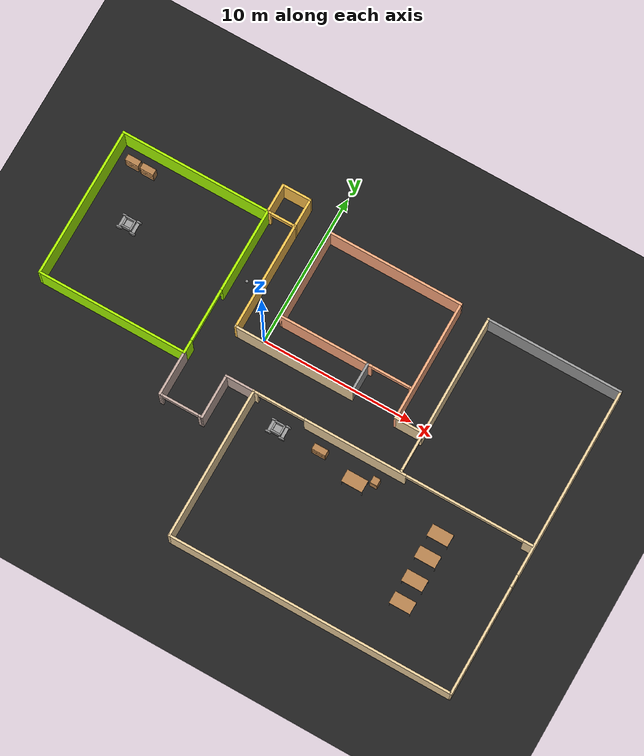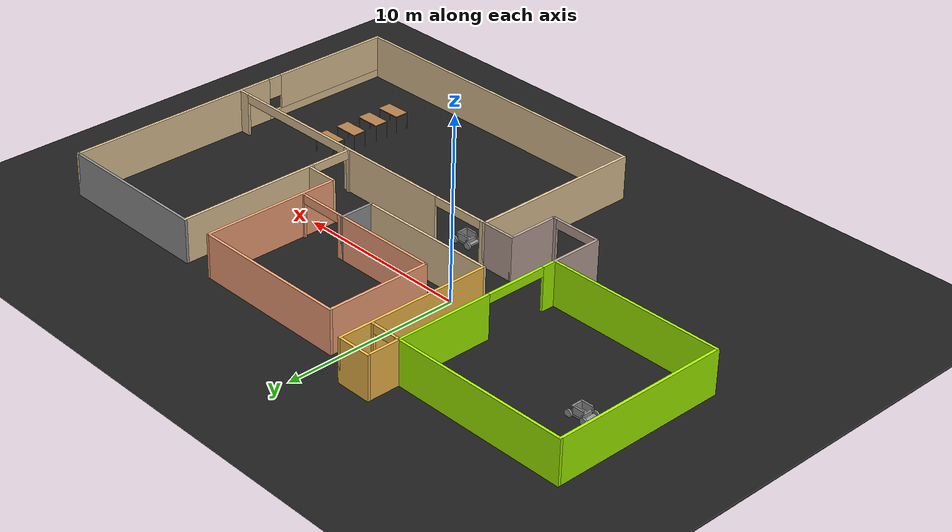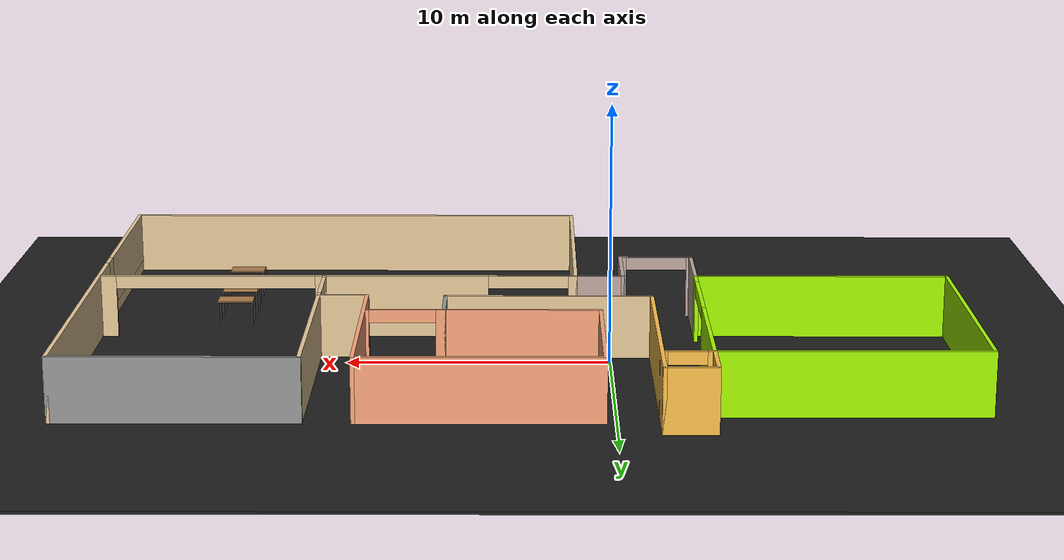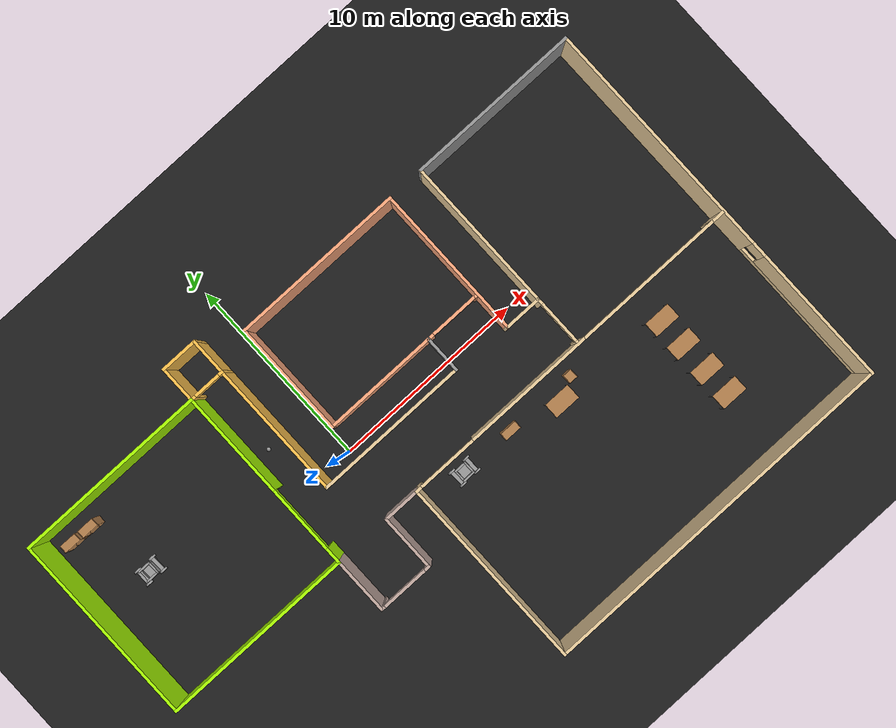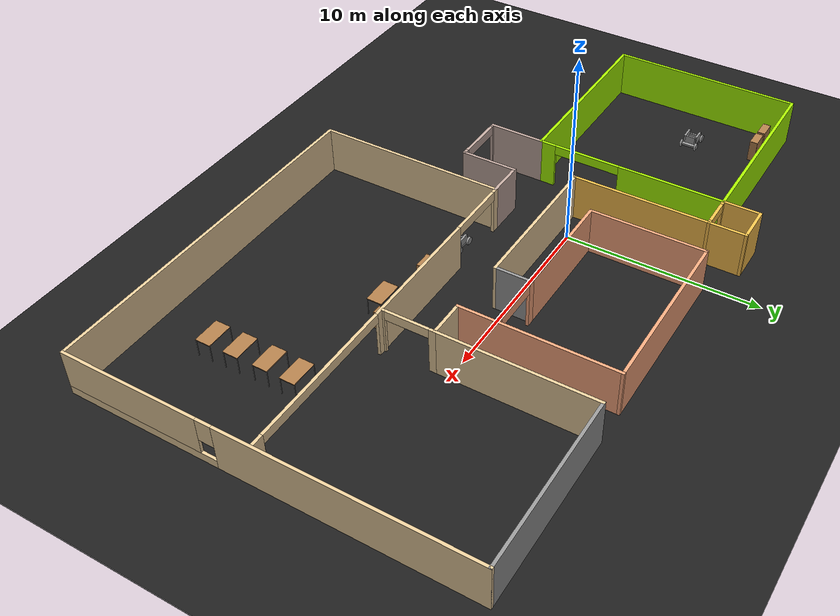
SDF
<sdf version="1.6">
 <world name="default">
  <plugin name="welcome_message" filename="libwelcome_message.so"/>
  <light name="sun" type="directional">
   <pose>0 0 10 0 -0 0</pose>
   <diffuse>0.8 0.8 0.8 1</diffuse>
   <specular>0.1 0.1 0.1 1</specular>
   <attenuation>
    <range>1000</range>
    <constant>0.9</constant>
    <linear>0.01</linear>
    <quadratic>0.001</quadratic>
   </attenuation>
   <direction>-0.5 0.5 -1</direction>
  </light>
  <model name="ground_plane">
   <static>1</static>
   <link name="link">
    <collision name="collision">
     <geometry><plane><normal>0 0 1</normal><size>100 100</size></plane></geometry>
     <surface><friction><ode><mu>100</mu><mu2>50</mu2></ode></friction></surface>
    </collision>
    <visual name="visual">
     <cast_shadows>0</cast_shadows>
     <geometry><plane><normal>0 0 1</normal><size>100 100</size></plane></geometry>
     <material>
      <script><uri>file://media/materials/scripts/gazebo.material</uri><name>Gazebo/FlatBlack</name></script>
     </material>
    </visual>
   </link>
  </model>
  <gravity>0 0 -9.8</gravity>
  <magnetic_field>6e-06 2.3e-05 -4.2e-05</magnetic_field>
  <atmosphere type="adiabatic"/>
  <physics name="default_physics" default="0" type="ode">
   <max_step_size>0.001</max_step_size>
   <real_time_factor>1</real_time_factor>
   <real_time_update_rate>1000</real_time_update_rate>
  </physics>
  <scene><ambient>0.4 0.4 0.4 1</ambient><background>0.7 0.7 0.7 1</background><shadows>1</shadows></scene>
  <spherical_coordinates>
   <surface_model>EARTH_WGS84</surface_model>
   <latitude_deg>0</latitude_deg>
   <longitude_deg>0</longitude_deg>
   <elevation>0</elevation>
   <heading_deg>0</heading_deg>
  </spherical_coordinates>
  <model name="myhouse.config">
   <pose>3.332 -2.461 0 0 -0 0</pose>
   <link name="Wall_15">
    <collision name="Wall_15_Collision">
     <geometry><box><size>9 0.15 2.5</size></box></geometry>
     <pose>0 0 1.25 0 -0 0</pose>
    </collision>
    <visual name="Wall_15_Visual">
     <pose>0 0 1.25 0 -0 0</pose>
     <geometry><box><size>9 0.15 2.5</size></box></geometry>
     <material>
      <script><uri>file://media/materials/scripts/gazebo.material</uri><name>Gazebo/Grey</name></script>
      <ambient>1 1 1 1</ambient>
     </material>
    </visual>
    <pose>12.2 9.625 0 0 -0 3.14159</pose>
   </link>
   <link name="Wall_17">
    <collision name="Wall_17_Collision">
     <geometry><box><size>8 0.15 2.5</size></box></geometry>
     <pose>0 0 1.25 0 -0 0</pose>
    </collision>
    <visual name="Wall_17_Visual">
     <pose>0 0 1.25 0 -0 0</pose>
     <geometry><box><size>8 0.15 2.5</size></box></geometry>
     <material>
      <script><uri>file://media/materials/scripts/gazebo.material</uri><name>Gazebo/Grey</name></script>
      <ambient>0.921569 0.807843 0.615686 1</ambient>
     </material>
    </visual>
    <pose>7.775 5.7 0 0 0 -1.5708</pose>
   </link>
   <link name="Wall_19">
    <collision name="Wall_19_Collision">
     <geometry><box><size>2 0.15 2.5</size></box></geometry>
     <pose>0 0 1.25 0 -0 0</pose>
    </collision>
    <visual name="Wall_19_Visual">
     <pose>0 0 1.25 0 -0 0</pose>
     <geometry><box><size>2 0.15 2.5</size></box></geometry>
     <material>
      <script><uri>file://media/materials/scripts/gazebo.material</uri><name>Gazebo/Grey</name></script>
      <ambient>0.921569 0.807843 0.615686 1</ambient>
     </material>
    </visual>
    <pose>6.85 1.775 0 0 -0 3.14159</pose>
   </link>
   <link name="Wall_20">
    <collision name="Wall_20_Collision">
     <geometry><box><size>8 0.15 2.5</size></box></geometry>
     <pose>0 0 1.25 0 -0 0</pose>
    </collision>
    <visual name="Wall_20_Visual">
     <pose>0 0 1.25 0 -0 0</pose>
     <geometry><box><size>8 0.15 2.5</size></box></geometry>
     <material>
      <script><uri>file://media/materials/scripts/gazebo.material</uri><name>Gazebo/Grey</name></script>
      <ambient>1 0.666667 0.498039 1</ambient>
     </material>
    </visual>
    <pose>5.925 5.7 0 0 -0 1.5708</pose>
   </link>
   <link name="Wall_22">
    <collision name="Wall_22_Collision">
     <geometry><box><size>9 0.15 2.5</size></box></geometry>
     <pose>0 0 1.25 0 -0 0</pose>
    </collision>
    <visual name="Wall_22_Visual">
     <pose>0 0 1.25 0 -0 0</pose>
     <geometry><box><size>9 0.15 2.5</size></box></geometry>
     <material>
      <script><uri>file://media/materials/scripts/gazebo.material</uri><name>Gazebo/Grey</name></script>
      <ambient>1 0.666667 0.498039 1</ambient>
     </material>
    </visual>
    <pose>1.5 9.625 0 0 -0 3.14159</pose>
   </link>
   <link name="Wall_24">
    <collision name="Wall_24_Collision">
     <geometry><box><size>6 0.15 2.5</size></box></geometry>
     <pose>0 0 1.25 0 -0 0</pose>
    </collision>
    <visual name="Wall_24_Visual">
     <pose>0 0 1.25 0 -0 0</pose>
     <geometry><box><size>6 0.15 2.5</size></box></geometry>
     <material>
      <script><uri>file://media/materials/scripts/gazebo.material</uri><name>Gazebo/Grey</name></script>
      <ambient>1 0.666667 0.498039 1</ambient>
     </material>
    </visual>
    <pose>-2.925 6.7 0 0 0 -1.5708</pose>
   </link>
   <link name="Wall_25">
    <collision name="Wall_25_Collision">
     <geometry><box><size>6 0.15 2.5</size></box></geometry>
     <pose>0 0 1.25 0 -0 0</pose>
    </collision>
    <visual name="Wall_25_Visual">
     <pose>0 0 1.25 0 -0 0</pose>
     <geometry><box><size>6 0.15 2.5</size></box></geometry>
     <material>
      <script><uri>file://media/materials/scripts/gazebo.material</uri><name>Gazebo/Grey</name></script>
      <ambient>1 0.666667 0.498039 1</ambient>
     </material>
    </visual>
    <pose>0 3.775 0 0 -0 0</pose>
   </link>
   <link name="Wall_26">
    <collision name="Wall_26_Collision">
     <geometry><box><size>2 0.15 2.5</size></box></geometry>
     <pose>0 0 1.25 0 -0 0</pose>
    </collision>
    <visual name="Wall_26_Visual">
     <pose>0 0 1.25 0 -0 0</pose>
     <geometry><box><size>2 0.15 2.5</size></box></geometry>
     <material>
      <script><uri>file://media/materials/scripts/gazebo.material</uri><name>Gazebo/Grey</name></script>
      <ambient>1 1 1 1</ambient>
     </material>
    </visual>
    <pose>2.925 2.85 0 0 0 -1.5708</pose>
   </link>
   <link name="Wall_27">
    <collision name="Wall_27_Collision">
     <geometry><box><size>8 0.15 2.5</size></box></geometry>
     <pose>0 0 1.25 0 -0 0</pose>
    </collision>
    <visual name="Wall_27_Visual">
     <pose>0 0 1.25 0 -0 0</pose>
     <geometry><box><size>8 0.15 2.5</size></box></geometry>
     <material>
      <script><uri>file://media/materials/scripts/gazebo.material</uri><name>Gazebo/Grey</name></script>
      <ambient>0.921569 0.807843 0.615686 1</ambient>
     </material>
    </visual>
    <pose>-1 1.925 0 0 -0 3.14159</pose>
   </link>
   <link name="Wall_28">
    <collision name="Wall_28_Collision">
     <geometry><box><size>9 0.15 2.5</size></box></geometry>
     <pose>0 0 1.25 0 -0 0</pose>
    </collision>
    <visual name="Wall_28_Visual">
     <pose>0 0 1.25 0 -0 0</pose>
     <geometry><box><size>9 0.15 2.5</size></box></geometry>
     <material>
      <script><uri>file://media/materials/scripts/gazebo.material</uri><name>Gazebo/Grey</name></script>
      <ambient>1 0.764706 0.305882 1</ambient>
     </material>
    </visual>
    <pose>-4.925 6.35 0 0 -0 1.5708</pose>
   </link>
   <link name="Wall_29">
    <collision name="Wall_29_Collision">
     <geometry><box><size>2 0.15 2.5</size></box></geometry>
     <pose>0 0 1.25 0 -0 0</pose>
    </collision>
    <visual name="Wall_29_Visual">
     <pose>0 0 1.25 0 -0 0</pose>
     <geometry><box><size>2 0.15 2.5</size></box></geometry>
     <material>
      <script><uri>file://media/materials/scripts/gazebo.material</uri><name>Gazebo/Grey</name></script>
      <ambient>1 0.764706 0.305882 1</ambient>
     </material>
    </visual>
    <pose>-5.85 10.775 0 0 -0 3.14159</pose>
   </link>
   <link name="Wall_30">
    <collision name="Wall_30_Collision">
     <geometry><box><size>2 0.15 2.5</size></box></geometry>
     <pose>0 0 1.25 0 -0 0</pose>
    </collision>
    <visual name="Wall_30_Visual">
     <pose>0 0 1.25 0 -0 0</pose>
     <geometry><box><size>2 0.15 2.5</size></box></geometry>
     <material>
      <script><uri>file://media/materials/scripts/gazebo.material</uri><name>Gazebo/Grey</name></script>
      <ambient>1 0.764706 0.305882 1</ambient>
     </material>
    </visual>
    <pose>-6.775 9.85 0 0 0 -1.5708</pose>
   </link>
   <link name="Wall_31">
    <collision name="Wall_31_Collision">
     <geometry><box><size>10 0.15 2.5</size></box></geometry>
     <pose>0 0 1.25 0 -0 0</pose>
    </collision>
    <visual name="Wall_31_Visual">
     <pose>0 0 1.25 0 -0 0</pose>
     <geometry><box><size>10 0.15 2.5</size></box></geometry>
     <material>
      <script><uri>file://media/materials/scripts/gazebo.material</uri><name>Gazebo/Grey</name></script>
      <ambient>0.666667 1 0 1</ambient>
     </material>
    </visual>
    <pose>-11.7 8.925 0 0 -0 3.14159</pose>
   </link>
   <link name="Wall_32">
    <collision name="Wall_32_Collision">
     <geometry><box><size>10 0.15 2.5</size></box></geometry>
     <pose>0 0 1.25 0 -0 0</pose>
    </collision>
    <visual name="Wall_32_Visual">
     <pose>0 0 1.25 0 -0 0</pose>
     <geometry><box><size>10 0.15 2.5</size></box></geometry>
     <material>
      <script><uri>file://media/materials/scripts/gazebo.material</uri><name>Gazebo/Grey</name></script>
      <ambient>0.666667 1 0 1</ambient>
     </material>
    </visual>
    <pose>-16.625 4 0 0 0 -1.5708</pose>
   </link>
   <link name="Wall_33">
    <collision name="Wall_33_Collision">
     <geometry><box><size>10 0.15 2.5</size></box></geometry>
     <pose>0 0 1.25 0 -0 0</pose>
    </collision>
    <visual name="Wall_33_Visual">
     <pose>0 0 1.25 0 -0 0</pose>
     <geometry><box><size>10 0.15 2.5</size></box></geometry>
     <material>
      <script><uri>file://media/materials/scripts/gazebo.material</uri><name>Gazebo/Grey</name></script>
      <ambient>0.666667 1 0 1</ambient>
     </material>
    </visual>
    <pose>-11.7 -0.924999 0 0 -0 0</pose>
   </link>
   <link name="Wall_34">
    <collision name="Wall_34_Collision">
     <geometry><box><size>3 0.15 2.5</size></box></geometry>
     <pose>0 0 1.25 0 -0 0</pose>
    </collision>
    <visual name="Wall_34_Visual">
     <pose>0 0 1.25 0 -0 0</pose>
     <geometry><box><size>3 0.15 2.5</size></box></geometry>
     <material>
      <script><uri>file://media/materials/scripts/gazebo.material</uri><name>Gazebo/Grey</name></script>
      <ambient>0.760784 0.662745 0.627451 1</ambient>
     </material>
    </visual>
    <pose>-6.775 -2.35 0 0 0 -1.5708</pose>
   </link>
   <link name="Wall_35">
    <pose>-5.35 -3.775 0 0 -0 0</pose>
    <visual name="Wall_35_Visual_0">
     <pose>-1.3701 0 1.25 0 -0 0</pose>
     <geometry><box><size>0.259804 0.15 2.5</size></box></geometry>
     <material>
      <script><uri>file://media/materials/scripts/gazebo.material</uri><name>Gazebo/Grey</name></script>
      <ambient>0.760784 0.662745 0.627451 1</ambient>
     </material>
    </visual>
    <collision name="Wall_35_Collision_0">
     <geometry><box><size>0.259804 0.15 2.5</size></box></geometry>
     <pose>-1.3701 0 1.25 0 -0 0</pose>
    </collision>
    <visual name="Wall_35_Visual_1">
     <pose>1.33743 0 1.25 0 -0 0</pose>
     <geometry><box><size>0.325141 0.15 2.5</size></box></geometry>
     <material>
      <script><uri>file://media/materials/scripts/gazebo.material</uri><name>Gazebo/Grey</name></script>
      <ambient>0.760784 0.662745 0.627451 1</ambient>
     </material>
    </visual>
    <collision name="Wall_35_Collision_1">
     <geometry><box><size>0.325141 0.15 2.5</size></box></geometry>
     <pose>1.33743 0 1.25 0 -0 0</pose>
    </collision>
    <visual name="Wall_35_Visual_2">
     <pose>-0.032669 0 2.25 0 -0 0</pose>
     <geometry><box><size>2.41506 0.15 0.5</size></box></geometry>
     <material>
      <script><uri>file://media/materials/scripts/gazebo.material</uri><name>Gazebo/Grey</name></script>
      <ambient>0.760784 0.662745 0.627451 1</ambient>
     </material>
    </visual>
    <collision name="Wall_35_Collision_2">
     <geometry><box><size>2.41506 0.15 0.5</size></box></geometry>
     <pose>-0.032669 0 2.25 0 -0 0</pose>
    </collision>
   </link>
   <link name="Wall_36">
    <collision name="Wall_36_Collision">
     <geometry><box><size>3 0.15 2.5</size></box></geometry>
     <pose>0 0 1.25 0 -0 0</pose>
    </collision>
    <visual name="Wall_36_Visual">
     <pose>0 0 1.25 0 -0 0</pose>
     <geometry><box><size>3 0.15 2.5</size></box></geometry>
     <material>
      <script><uri>file://media/materials/scripts/gazebo.material</uri><name>Gazebo/Grey</name></script>
      <ambient>0.760784 0.662745 0.627451 1</ambient>
     </material>
    </visual>
    <pose>-3.925 -2.35 0 0 -0 1.5708</pose>
   </link>
   <link name="Wall_37">
    <collision name="Wall_37_Collision">
     <geometry><box><size>2 0.15 2.5</size></box></geometry>
     <pose>0 0 1.25 0 -0 0</pose>
    </collision>
    <visual name="Wall_37_Visual">
     <pose>0 0 1.25 0 -0 0</pose>
     <geometry><box><size>2 0.15 2.5</size></box></geometry>
     <material>
      <script><uri>file://media/materials/scripts/gazebo.material</uri><name>Gazebo/Grey</name></script>
      <ambient>0.760784 0.662745 0.627451 1</ambient>
     </material>
    </visual>
    <pose>-3 -0.924999 0 0 -0 0</pose>
   </link>
   <link name="Wall_40">
    <pose>16.625 -0.575 0 0 0 -1.5708</pose>
    <visual name="Wall_40_Visual_0">
     <pose>-3.99354 0 1.25 0 -0 0</pose>
     <geometry><box><size>12.5629 0.15 2.5</size></box></geometry>
     <material>
      <script><uri>file://media/materials/scripts/gazebo.material</uri><name>Gazebo/Grey</name></script>
      <ambient>0.921569 0.807843 0.615686 1</ambient>
     </material>
    </visual>
    <collision name="Wall_40_Collision_0">
     <geometry><box><size>12.5629 0.15 2.5</size></box></geometry>
     <pose>-3.99354 0 1.25 0 -0 0</pose>
    </collision>
    <visual name="Wall_40_Visual_1">
     <pose>6.28146 0 0.25 0 -0 0</pose>
     <geometry><box><size>7.98707 0.15 0.5</size></box></geometry>
     <material>
      <script><uri>file://media/materials/scripts/gazebo.material</uri><name>Gazebo/Grey</name></script>
      <ambient>0.921569 0.807843 0.615686 1</ambient>
     </material>
    </visual>
    <collision name="Wall_40_Collision_1">
     <geometry><box><size>7.98707 0.15 0.5</size></box></geometry>
     <pose>6.28146 0 0.25 0 -0 0</pose>
    </collision>
    <visual name="Wall_40_Visual_2">
     <pose>6.68146 0 1.5 0 -0 0</pose>
     <geometry><box><size>7.18707 0.15 2</size></box></geometry>
     <material>
      <script><uri>file://media/materials/scripts/gazebo.material</uri><name>Gazebo/Grey</name></script>
      <ambient>0.921569 0.807843 0.615686 1</ambient>
     </material>
    </visual>
    <collision name="Wall_40_Collision_2">
     <geometry><box><size>7.18707 0.15 2</size></box></geometry>
     <pose>6.68146 0 1.5 0 -0 0</pose>
    </collision>
    <visual name="Wall_40_Visual_3">
     <pose>2.68793 0 1.9 0 -0 0</pose>
     <geometry><box><size>0.8 0.15 1.2</size></box></geometry>
     <material>
      <script><uri>file://media/materials/scripts/gazebo.material</uri><name>Gazebo/Grey</name></script>
      <ambient>0.921569 0.807843 0.615686 1</ambient>
     </material>
    </visual>
    <collision name="Wall_40_Collision_3">
     <geometry><box><size>0.8 0.15 1.2</size></box></geometry>
     <pose>2.68793 0 1.9 0 -0 0</pose>
    </collision>
   </link>
   <link name="Wall_42">
    <collision name="Wall_42_Collision">
     <geometry><box><size>10 0.15 2.5</size></box></geometry>
     <pose>0 0 1.25 0 -0 0</pose>
    </collision>
    <visual name="Wall_42_Visual">
     <pose>0 0 1.25 0 -0 0</pose>
     <geometry><box><size>10 0.15 2.5</size></box></geometry>
     <material>
      <script><uri>file://media/materials/scripts/gazebo.material</uri><name>Gazebo/Grey</name></script>
      <ambient>0.921569 0.807843 0.615686 1</ambient>
     </material>
    </visual>
    <pose>-2.075 -5.85 0 0 0 -1.5708</pose>
   </link>
   <link name="Wall_44">
    <collision name="Wall_44_Collision">
     <geometry><box><size>18.75 0.15 2.5</size></box></geometry>
     <pose>0 0 1.25 0 -0 0</pose>
    </collision>
    <visual name="Wall_44_Visual">
     <pose>0 0 1.25 0 -0 0</pose>
     <geometry><box><size>18.75 0.15 2.5</size></box></geometry>
     <material>
      <script><uri>file://media/materials/scripts/gazebo.material</uri><name>Gazebo/Grey</name></script>
      <ambient>0.921569 0.807843 0.615686 1</ambient>
     </material>
    </visual>
    <pose>7.225 -10.775 0 0 -0 0</pose>
   </link>
   <link name="Wall_46">
    <pose>-6.775 4 0 0 0 -1.5708</pose>
    <visual name="Wall_46_Visual_0">
     <pose>-2.20451 0 1.25 0 -0 0</pose>
     <geometry><box><size>5.59098 0.15 2.5</size></box></geometry>
     <material>
      <script><uri>file://media/materials/scripts/gazebo.material</uri><name>Gazebo/Grey</name></script>
      <ambient>0.666667 1 0 1</ambient>
     </material>
    </visual>
    <collision name="Wall_46_Collision_0">
     <geometry><box><size>5.59098 0.15 2.5</size></box></geometry>
     <pose>-2.20451 0 1.25 0 -0 0</pose>
    </collision>
    <visual name="Wall_46_Visual_1">
     <pose>4.5489 0 1.25 0 -0 0</pose>
     <geometry><box><size>0.902202 0.15 2.5</size></box></geometry>
     <material>
      <script><uri>file://media/materials/scripts/gazebo.material</uri><name>Gazebo/Grey</name></script>
      <ambient>0.666667 1 0 1</ambient>
     </material>
    </visual>
    <collision name="Wall_46_Collision_1">
     <geometry><box><size>0.902202 0.15 2.5</size></box></geometry>
     <pose>4.5489 0 1.25 0 -0 0</pose>
    </collision>
    <visual name="Wall_46_Visual_2">
     <pose>2.34439 0 2.25 0 -0 0</pose>
     <geometry><box><size>3.50682 0.15 0.5</size></box></geometry>
     <material>
      <script><uri>file://media/materials/scripts/gazebo.material</uri><name>Gazebo/Grey</name></script>
      <ambient>0.666667 1 0 1</ambient>
     </material>
    </visual>
    <collision name="Wall_46_Collision_2">
     <geometry><box><size>3.50682 0.15 0.5</size></box></geometry>
     <pose>2.34439 0 2.25 0 -0 0</pose>
    </collision>
   </link>
   <link name="Wall_48">
    <pose>7.225 -0.924999 0 0 -0 0</pose>
    <visual name="Wall_48_Visual_0">
     <pose>-9.19055 0 1.25 0 -0 0</pose>
     <geometry><box><size>0.3689 0.15 2.5</size></box></geometry>
     <material>
      <script><uri>file://media/materials/scripts/gazebo.material</uri><name>Gazebo/Grey</name></script>
      <ambient>0.921569 0.807843 0.615686 1</ambient>
     </material>
    </visual>
    <collision name="Wall_48_Collision_0">
     <geometry><box><size>0.3689 0.15 2.5</size></box></geometry>
     <pose>-9.19055 0 1.25 0 -0 0</pose>
    </collision>
    <visual name="Wall_48_Visual_1">
     <pose>-2.48259 0 1.25 0 -0 0</pose>
     <geometry><box><size>6.80594 0.15 2.5</size></box></geometry>
     <material>
      <script><uri>file://media/materials/scripts/gazebo.material</uri><name>Gazebo/Grey</name></script>
      <ambient>0.921569 0.807843 0.615686 1</ambient>
     </material>
    </visual>
    <collision name="Wall_48_Collision_1">
     <geometry><box><size>6.80594 0.15 2.5</size></box></geometry>
     <pose>-2.48259 0 1.25 0 -0 0</pose>
    </collision>
    <visual name="Wall_48_Visual_2">
     <pose>9.04701 0 1.25 0 -0 0</pose>
     <geometry><box><size>0.655974 0.15 2.5</size></box></geometry>
     <material>
      <script><uri>file://media/materials/scripts/gazebo.material</uri><name>Gazebo/Grey</name></script>
      <ambient>0.921569 0.807843 0.615686 1</ambient>
     </material>
    </visual>
    <collision name="Wall_48_Collision_2">
     <geometry><box><size>0.655974 0.15 2.5</size></box></geometry>
     <pose>9.04701 0 1.25 0 -0 0</pose>
    </collision>
    <visual name="Wall_48_Visual_3">
     <pose>-7.44583 0 2.25 0 -0 0</pose>
     <geometry><box><size>3.12054 0.15 0.5</size></box></geometry>
     <material>
      <script><uri>file://media/materials/scripts/gazebo.material</uri><name>Gazebo/Grey</name></script>
      <ambient>0.921569 0.807843 0.615686 1</ambient>
     </material>
    </visual>
    <collision name="Wall_48_Collision_3">
     <geometry><box><size>3.12054 0.15 0.5</size></box></geometry>
     <pose>-7.44583 0 2.25 0 -0 0</pose>
    </collision>
    <visual name="Wall_48_Visual_4">
     <pose>4.8197 0 2.25 0 -0 0</pose>
     <geometry><box><size>7.79865 0.15 0.5</size></box></geometry>
     <material>
      <script><uri>file://media/materials/scripts/gazebo.material</uri><name>Gazebo/Grey</name></script>
      <ambient>0.921569 0.807843 0.615686 1</ambient>
     </material>
    </visual>
    <collision name="Wall_48_Collision_4">
     <geometry><box><size>7.79865 0.15 0.5</size></box></geometry>
     <pose>4.8197 0 2.25 0 -0 0</pose>
    </collision>
   </link>
   <link name="Wall_50">
    <pose>7.775 0.475001 0 0 0 -1.5708</pose>
    <visual name="Wall_50_Visual_0">
     <pose>-1.19597 0 1.25 0 -0 0</pose>
     <geometry><box><size>0.358051 0.15 2.5</size></box></geometry>
     <material>
      <script><uri>file://media/materials/scripts/gazebo.material</uri><name>Gazebo/Grey</name></script>
      <ambient>0.921569 0.807843 0.615686 1</ambient>
     </material>
    </visual>
    <collision name="Wall_50_Collision_0">
     <geometry><box><size>0.358051 0.15 2.5</size></box></geometry>
     <pose>-1.19597 0 1.25 0 -0 0</pose>
    </collision>
    <visual name="Wall_50_Visual_1">
     <pose>1.29981 0 1.25 0 -0 0</pose>
     <geometry><box><size>0.150373 0.15 2.5</size></box></geometry>
     <material>
      <script><uri>file://media/materials/scripts/gazebo.material</uri><name>Gazebo/Grey</name></script>
      <ambient>0.921569 0.807843 0.615686 1</ambient>
     </material>
    </visual>
    <collision name="Wall_50_Collision_1">
     <geometry><box><size>0.150373 0.15 2.5</size></box></geometry>
     <pose>1.29981 0 1.25 0 -0 0</pose>
    </collision>
    <visual name="Wall_50_Visual_2">
     <pose>0.103839 0 2.25 0 -0 0</pose>
     <geometry><box><size>2.24158 0.15 0.5</size></box></geometry>
     <material>
      <script><uri>file://media/materials/scripts/gazebo.material</uri><name>Gazebo/Grey</name></script>
      <ambient>0.921569 0.807843 0.615686 1</ambient>
     </material>
    </visual>
    <collision name="Wall_50_Collision_2">
     <geometry><box><size>2.24158 0.15 0.5</size></box></geometry>
     <pose>0.103839 0 2.25 0 -0 0</pose>
    </collision>
   </link>
   <link name="Wall_52">
    <pose>4.35 3.775 0 0 -0 0</pose>
    <visual name="Wall_52_Visual_0">
     <pose>-1.30967 0 1.25 0 -0 0</pose>
     <geometry><box><size>0.380655 0.15 2.5</size></box></geometry>
     <material>
      <script><uri>file://media/materials/scripts/gazebo.material</uri><name>Gazebo/Grey</name></script>
      <ambient>1 0.666667 0.498039 1</ambient>
     </material>
    </visual>
    <collision name="Wall_52_Collision_0">
     <geometry><box><size>0.380655 0.15 2.5</size></box></geometry>
     <pose>-1.30967 0 1.25 0 -0 0</pose>
    </collision>
    <visual name="Wall_52_Visual_1">
     <pose>1.43833 0 1.25 0 -0 0</pose>
     <geometry><box><size>0.123333 0.15 2.5</size></box></geometry>
     <material>
      <script><uri>file://media/materials/scripts/gazebo.material</uri><name>Gazebo/Grey</name></script>
      <ambient>1 0.666667 0.498039 1</ambient>
     </material>
    </visual>
    <collision name="Wall_52_Collision_1">
     <geometry><box><size>0.123333 0.15 2.5</size></box></geometry>
     <pose>1.43833 0 1.25 0 -0 0</pose>
    </collision>
    <visual name="Wall_52_Visual_2">
     <pose>0.128661 0 2.25 0 -0 0</pose>
     <geometry><box><size>2.49601 0.15 0.5</size></box></geometry>
     <material>
      <script><uri>file://media/materials/scripts/gazebo.material</uri><name>Gazebo/Grey</name></script>
      <ambient>1 0.666667 0.498039 1</ambient>
     </material>
    </visual>
    <collision name="Wall_52_Collision_2">
     <geometry><box><size>2.49601 0.15 0.5</size></box></geometry>
     <pose>0.128661 0 2.25 0 -0 0</pose>
    </collision>
   </link>
   <link name="Wall_54">
    <pose>-5.85 8.925 0 0 -0 0</pose>
    <visual name="Wall_54_Visual_0">
     <pose>-0.84004 0 1.25 0 -0 0</pose>
     <geometry><box><size>0.319921 0.15 2.5</size></box></geometry>
     <material>
      <script><uri>file://media/materials/scripts/gazebo.material</uri><name>Gazebo/Grey</name></script>
      <ambient>1 0.764706 0.305882 1</ambient>
     </material>
    </visual>
    <collision name="Wall_54_Collision_0">
     <geometry><box><size>0.319921 0.15 2.5</size></box></geometry>
     <pose>-0.84004 0 1.25 0 -0 0</pose>
    </collision>
    <visual name="Wall_54_Visual_1">
     <pose>0.862662 0 1.25 0 -0 0</pose>
     <geometry><box><size>0.274676 0.15 2.5</size></box></geometry>
     <material>
      <script><uri>file://media/materials/scripts/gazebo.material</uri><name>Gazebo/Grey</name></script>
      <ambient>1 0.764706 0.305882 1</ambient>
     </material>
    </visual>
    <collision name="Wall_54_Collision_1">
     <geometry><box><size>0.274676 0.15 2.5</size></box></geometry>
     <pose>0.862662 0 1.25 0 -0 0</pose>
    </collision>
    <visual name="Wall_54_Visual_2">
     <pose>0.022623 0 2.25 0 -0 0</pose>
     <geometry><box><size>1.4054 0.15 0.5</size></box></geometry>
     <material>
      <script><uri>file://media/materials/scripts/gazebo.material</uri><name>Gazebo/Grey</name></script>
      <ambient>1 0.764706 0.305882 1</ambient>
     </material>
    </visual>
    <collision name="Wall_54_Collision_2">
     <geometry><box><size>1.4054 0.15 0.5</size></box></geometry>
     <pose>0.022623 0 2.25 0 -0 0</pose>
    </collision>
   </link>
   <static>1</static>
  </model>
  <model name="ground_plane_0">
   <static>1</static>
   <link name="link">
    <collision name="collision">
     <geometry><plane><normal>0 0 1</normal><size>100 100</size></plane></geometry>
     <surface><friction><ode><mu>100</mu><mu2>50</mu2></ode></friction></surface>
    </collision>
    <visual name="visual">
     <cast_shadows>0</cast_shadows>
     <geometry><plane><normal>0 0 1</normal><size>100 100</size></plane></geometry>
     <material>
      <script><uri>file://media/materials/scripts/gazebo.material</uri><name>Gazebo/FlatBlack</name></script>
     </material>
    </visual>
   </link>
   <pose>5.89907 11.0236 0 0 -0 0</pose>
  </model>
  <light name="sun_0" type="directional">
   <pose>13.3795 97.3207 10 0 -0 0</pose>
   <diffuse>0.8 0.8 0.8 1</diffuse>
   <specular>0.1 0.1 0.1 1</specular>
   <attenuation>
    <range>1000</range>
    <constant>0.9</constant>
    <linear>0.01</linear>
    <quadratic>0.001</quadratic>
   </attenuation>
   <direction>-0.5 0.5 -1</direction>
  </light>
  <model name="bookshelf">
   <static>1</static>
   <link name="link">
    <inertial><mass>1</mass></inertial>
    <collision name="back">
     <pose>0 0.005 0.6 0 -0 0</pose>
     <geometry><box><size>0.9 0.01 1.2</size></box></geometry>
    </collision>
    <visual name="visual1">
     <pose>0 0.005 0.6 0 -0 0</pose>
     <geometry><box><size>0.9 0.01 1.2</size></box></geometry>
     <material>
      <script><uri>file://media/materials/scripts/gazebo.material</uri><name>Gazebo/Wood</name></script>
     </material>
    </visual>
    <collision name="left_side">
     <pose>0.45 -0.195 0.6 0 -0 0</pose>
     <geometry><box><size>0.02 0.4 1.2</size></box></geometry>
    </collision>
    <visual name="visual2">
     <pose>0.45 -0.195 0.6 0 -0 0</pose>
     <geometry><box><size>0.02 0.4 1.2</size></box></geometry>
     <material>
      <script><uri>file://media/materials/scripts/gazebo.material</uri><name>Gazebo/Wood</name></script>
     </material>
    </visual>
    <collision name="right_side">
     <pose>-0.45 -0.195 0.6 0 -0 0</pose>
     <geometry><box><size>0.02 0.4 1.2</size></box></geometry>
    </collision>
    <visual name="visual3">
     <pose>-0.45 -0.195 0.6 0 -0 0</pose>
     <geometry><box><size>0.02 0.4 1.2</size></box></geometry>
     <material>
      <script><uri>file://media/materials/scripts/gazebo.material</uri><name>Gazebo/Wood</name></script>
     </material>
    </visual>
    <collision name="bottom">
     <pose>0 -0.195 0.03 0 -0 0</pose>
     <geometry><box><size>0.88 0.4 0.06</size></box></geometry>
    </collision>
    <visual name="visual4">
     <pose>0 -0.195 0.03 0 -0 0</pose>
     <geometry><box><size>0.88 0.4 0.06</size></box></geometry>
     <material>
      <script><uri>file://media/materials/scripts/gazebo.material</uri><name>Gazebo/Wood</name></script>
     </material>
    </visual>
    <collision name="top">
     <pose>0 -0.195 1.19 0 -0 0</pose>
     <geometry><box><size>0.88 0.4 0.02</size></box></geometry>
    </collision>
    <visual name="visual5">
     <pose>0 -0.195 1.19 0 -0 0</pose>
     <geometry><box><size>0.88 0.4 0.02</size></box></geometry>
     <material>
      <script><uri>file://media/materials/scripts/gazebo.material</uri><name>Gazebo/Wood</name></script>
     </material>
    </visual>
    <collision name="low_shelf">
     <pose>0 -0.195 0.43 0 -0 0</pose>
     <geometry><box><size>0.88 0.4 0.02</size></box></geometry>
    </collision>
    <visual name="visual6">
     <pose>0 -0.195 0.43 0 -0 0</pose>
     <geometry><box><size>0.88 0.4 0.02</size></box></geometry>
     <material>
      <script><uri>file://media/materials/scripts/gazebo.material</uri><name>Gazebo/Wood</name></script>
     </material>
    </visual>
    <collision name="high_shelf">
     <pose>0 -0.195 0.8 0 -0 0</pose>
     <geometry><box><size>0.88 0.4 0.02</size></box></geometry>
    </collision>
    <visual name="visual7">
     <pose>0 -0.195 0.8 0 -0 0</pose>
     <geometry><box><size>0.88 0.4 0.02</size></box></geometry>
     <material>
      <script><uri>file://media/materials/scripts/gazebo.material</uri><name>Gazebo/Wood</name></script>
     </material>
    </visual>
   </link>
   <pose>-12.1974 5.71971 0 0 -0 0</pose>
  </model>
  <model name="bookshelf_0">
   <static>1</static>
   <link name="link">
    <inertial><mass>1</mass></inertial>
    <collision name="back">
     <pose>0 0.005 0.6 0 -0 0</pose>
     <geometry><box><size>0.9 0.01 1.2</size></box></geometry>
    </collision>
    <visual name="visual1">
     <pose>0 0.005 0.6 0 -0 0</pose>
     <geometry><box><size>0.9 0.01 1.2</size></box></geometry>
     <material>
      <script><uri>file://media/materials/scripts/gazebo.material</uri><name>Gazebo/Wood</name></script>
     </material>
    </visual>
    <collision name="left_side">
     <pose>0.45 -0.195 0.6 0 -0 0</pose>
     <geometry><box><size>0.02 0.4 1.2</size></box></geometry>
    </collision>
    <visual name="visual2">
     <pose>0.45 -0.195 0.6 0 -0 0</pose>
     <geometry><box><size>0.02 0.4 1.2</size></box></geometry>
     <material>
      <script><uri>file://media/materials/scripts/gazebo.material</uri><name>Gazebo/Wood</name></script>
     </material>
    </visual>
    <collision name="right_side">
     <pose>-0.45 -0.195 0.6 0 -0 0</pose>
     <geometry><box><size>0.02 0.4 1.2</size></box></geometry>
    </collision>
    <visual name="visual3">
     <pose>-0.45 -0.195 0.6 0 -0 0</pose>
     <geometry><box><size>0.02 0.4 1.2</size></box></geometry>
     <material>
      <script><uri>file://media/materials/scripts/gazebo.material</uri><name>Gazebo/Wood</name></script>
     </material>
    </visual>
    <collision name="bottom">
     <pose>0 -0.195 0.03 0 -0 0</pose>
     <geometry><box><size>0.88 0.4 0.06</size></box></geometry>
    </collision>
    <visual name="visual4">
     <pose>0 -0.195 0.03 0 -0 0</pose>
     <geometry><box><size>0.88 0.4 0.06</size></box></geometry>
     <material>
      <script><uri>file://media/materials/scripts/gazebo.material</uri><name>Gazebo/Wood</name></script>
     </material>
    </visual>
    <collision name="top">
     <pose>0 -0.195 1.19 0 -0 0</pose>
     <geometry><box><size>0.88 0.4 0.02</size></box></geometry>
    </collision>
    <visual name="visual5">
     <pose>0 -0.195 1.19 0 -0 0</pose>
     <geometry><box><size>0.88 0.4 0.02</size></box></geometry>
     <material>
      <script><uri>file://media/materials/scripts/gazebo.material</uri><name>Gazebo/Wood</name></script>
     </material>
    </visual>
    <collision name="low_shelf">
     <pose>0 -0.195 0.43 0 -0 0</pose>
     <geometry><box><size>0.88 0.4 0.02</size></box></geometry>
    </collision>
    <visual name="visual6">
     <pose>0 -0.195 0.43 0 -0 0</pose>
     <geometry><box><size>0.88 0.4 0.02</size></box></geometry>
     <material>
      <script><uri>file://media/materials/scripts/gazebo.material</uri><name>Gazebo/Wood</name></script>
     </material>
    </visual>
    <collision name="high_shelf">
     <pose>0 -0.195 0.8 0 -0 0</pose>
     <geometry><box><size>0.88 0.4 0.02</size></box></geometry>
    </collision>
    <visual name="visual7">
     <pose>0 -0.195 0.8 0 -0 0</pose>
     <geometry><box><size>0.88 0.4 0.02</size></box></geometry>
     <material>
      <script><uri>file://media/materials/scripts/gazebo.material</uri><name>Gazebo/Wood</name></script>
     </material>
    </visual>
   </link>
   <pose>-11.1461 5.69388 0 0 -0 0</pose>
  </model>
  <model name="table_0">
   <static>0</static>
   <link name="link">
    <collision name="surface">
     <pose>0 0 1 0 -0 0</pose>
     <geometry><box><size>1.5 0.8 0.03</size></box></geometry>
     <surface><friction><ode><mu>0.6</mu><mu2>0.6</mu2></ode></friction></surface>
    </collision>
    <visual name="visual1">
     <pose>0 0 1 0 -0 0</pose>
     <geometry><box><size>1.4 0.8 0.04</size></box></geometry>
     <material>
      <script><uri>file://media/materials/scripts/gazebo.material</uri><name>Gazebo/Wood</name></script>
     </material>
    </visual>
    <collision name="front_left_leg">
     <pose>0.68 0.38 0.5 0 -0 0</pose>
     <geometry><cylinder><radius>0.02</radius><length>1</length></cylinder></geometry>
    </collision>
    <visual name="front_left_leg">
     <pose>0.68 0.38 0.5 0 -0 0</pose>
     <geometry><cylinder><radius>0.02</radius><length>1</length></cylinder></geometry>
     <material>
      <script><uri>file://media/materials/scripts/gazebo.material</uri><name>Gazebo/Grey</name></script>
     </material>
    </visual>
    <collision name="front_right_leg">
     <pose>0.68 -0.38 0.5 0 -0 0</pose>
     <geometry><cylinder><radius>0.02</radius><length>1</length></cylinder></geometry>
    </collision>
    <visual name="front_right_leg">
     <pose>0.68 -0.38 0.5 0 -0 0</pose>
     <geometry><cylinder><radius>0.02</radius><length>1</length></cylinder></geometry>
     <material>
      <script><uri>file://media/materials/scripts/gazebo.material</uri><name>Gazebo/Grey</name></script>
     </material>
    </visual>
    <collision name="back_right_leg">
     <pose>-0.68 -0.38 0.5 0 -0 0</pose>
     <geometry><cylinder><radius>0.02</radius><length>1</length></cylinder></geometry>
    </collision>
    <visual name="back_right_leg">
     <pose>-0.68 -0.38 0.5 0 -0 0</pose>
     <geometry><cylinder><radius>0.02</radius><length>1</length></cylinder></geometry>
     <material>
      <script><uri>file://media/materials/scripts/gazebo.material</uri><name>Gazebo/Grey</name></script>
     </material>
    </visual>
    <collision name="back_left_leg">
     <pose>-0.68 0.38 0.5 0 -0 0</pose>
     <geometry><cylinder><radius>0.02</radius><length>1</length></cylinder></geometry>
    </collision>
    <visual name="back_left_leg">
     <pose>-0.68 0.38 0.5 0 -0 0</pose>
     <geometry><cylinder><radius>0.02</radius><length>1</length></cylinder></geometry>
     <material>
      <script><uri>file://media/materials/scripts/gazebo.material</uri><name>Gazebo/Grey</name></script>
     </material>
    </visual>
    <inertial>
     <inertia><ixx>1</ixx><ixy>0</ixy><ixz>0</ixz><iyy>1</iyy><iyz>0</iyz><izz>1</izz></inertia>
     <mass>1</mass>
    </inertial>
   </link>
   <pose>14.8404 -5.25437 -8e-06 0 -2e-06 0</pose>
  </model>
  <model name="table_1">
   <static>0</static>
   <link name="link">
    <collision name="surface">
     <pose>0 0 1 0 -0 0</pose>
     <geometry><box><size>1.5 0.8 0.03</size></box></geometry>
     <surface><friction><ode><mu>0.6</mu><mu2>0.6</mu2></ode></friction></surface>
    </collision>
    <visual name="visual1">
     <pose>0 0 1 0 -0 0</pose>
     <geometry><box><size>1.4 0.8 0.04</size></box></geometry>
     <material>
      <script><uri>file://media/materials/scripts/gazebo.material</uri><name>Gazebo/Wood</name></script>
     </material>
    </visual>
    <collision name="front_left_leg">
     <pose>0.68 0.38 0.5 0 -0 0</pose>
     <geometry><cylinder><radius>0.02</radius><length>1</length></cylinder></geometry>
    </collision>
    <visual name="front_left_leg">
     <pose>0.68 0.38 0.5 0 -0 0</pose>
     <geometry><cylinder><radius>0.02</radius><length>1</length></cylinder></geometry>
     <material>
      <script><uri>file://media/materials/scripts/gazebo.material</uri><name>Gazebo/Grey</name></script>
     </material>
    </visual>
    <collision name="front_right_leg">
     <pose>0.68 -0.38 0.5 0 -0 0</pose>
     <geometry><cylinder><radius>0.02</radius><length>1</length></cylinder></geometry>
    </collision>
    <visual name="front_right_leg">
     <pose>0.68 -0.38 0.5 0 -0 0</pose>
     <geometry><cylinder><radius>0.02</radius><length>1</length></cylinder></geometry>
     <material>
      <script><uri>file://media/materials/scripts/gazebo.material</uri><name>Gazebo/Grey</name></script>
     </material>
    </visual>
    <collision name="back_right_leg">
     <pose>-0.68 -0.38 0.5 0 -0 0</pose>
     <geometry><cylinder><radius>0.02</radius><length>1</length></cylinder></geometry>
    </collision>
    <visual name="back_right_leg">
     <pose>-0.68 -0.38 0.5 0 -0 0</pose>
     <geometry><cylinder><radius>0.02</radius><length>1</length></cylinder></geometry>
     <material>
      <script><uri>file://media/materials/scripts/gazebo.material</uri><name>Gazebo/Grey</name></script>
     </material>
    </visual>
    <collision name="back_left_leg">
     <pose>-0.68 0.38 0.5 0 -0 0</pose>
     <geometry><cylinder><radius>0.02</radius><length>1</length></cylinder></geometry>
    </collision>
    <visual name="back_left_leg">
     <pose>-0.68 0.38 0.5 0 -0 0</pose>
     <geometry><cylinder><radius>0.02</radius><length>1</length></cylinder></geometry>
     <material>
      <script><uri>file://media/materials/scripts/gazebo.material</uri><name>Gazebo/Grey</name></script>
     </material>
    </visual>
    <inertial>
     <inertia><ixx>1</ixx><ixy>0</ixy><ixz>0</ixz><iyy>1</iyy><iyz>0</iyz><izz>1</izz></inertia>
     <mass>1</mass>
    </inertial>
   </link>
   <pose>14.8225 -6.72458 -8e-06 0 -2e-06 0</pose>
  </model>
  <model name="table_2">
   <static>0</static>
   <link name="link">
    <collision name="surface">
     <pose>0 0 1 0 -0 0</pose>
     <geometry><box><size>1.5 0.8 0.03</size></box></geometry>
     <surface><friction><ode><mu>0.6</mu><mu2>0.6</mu2></ode></friction></surface>
    </collision>
    <visual name="visual1">
     <pose>0 0 1 0 -0 0</pose>
     <geometry><box><size>1.4 0.8 0.04</size></box></geometry>
     <material>
      <script><uri>file://media/materials/scripts/gazebo.material</uri><name>Gazebo/Wood</name></script>
     </material>
    </visual>
    <collision name="front_left_leg">
     <pose>0.68 0.38 0.5 0 -0 0</pose>
     <geometry><cylinder><radius>0.02</radius><length>1</length></cylinder></geometry>
    </collision>
    <visual name="front_left_leg">
     <pose>0.68 0.38 0.5 0 -0 0</pose>
     <geometry><cylinder><radius>0.02</radius><length>1</length></cylinder></geometry>
     <material>
      <script><uri>file://media/materials/scripts/gazebo.material</uri><name>Gazebo/Grey</name></script>
     </material>
    </visual>
    <collision name="front_right_leg">
     <pose>0.68 -0.38 0.5 0 -0 0</pose>
     <geometry><cylinder><radius>0.02</radius><length>1</length></cylinder></geometry>
    </collision>
    <visual name="front_right_leg">
     <pose>0.68 -0.38 0.5 0 -0 0</pose>
     <geometry><cylinder><radius>0.02</radius><length>1</length></cylinder></geometry>
     <material>
      <script><uri>file://media/materials/scripts/gazebo.material</uri><name>Gazebo/Grey</name></script>
     </material>
    </visual>
    <collision name="back_right_leg">
     <pose>-0.68 -0.38 0.5 0 -0 0</pose>
     <geometry><cylinder><radius>0.02</radius><length>1</length></cylinder></geometry>
    </collision>
    <visual name="back_right_leg">
     <pose>-0.68 -0.38 0.5 0 -0 0</pose>
     <geometry><cylinder><radius>0.02</radius><length>1</length></cylinder></geometry>
     <material>
      <script><uri>file://media/materials/scripts/gazebo.material</uri><name>Gazebo/Grey</name></script>
     </material>
    </visual>
    <collision name="back_left_leg">
     <pose>-0.68 0.38 0.5 0 -0 0</pose>
     <geometry><cylinder><radius>0.02</radius><length>1</length></cylinder></geometry>
    </collision>
    <visual name="back_left_leg">
     <pose>-0.68 0.38 0.5 0 -0 0</pose>
     <geometry><cylinder><radius>0.02</radius><length>1</length></cylinder></geometry>
     <material>
      <script><uri>file://media/materials/scripts/gazebo.material</uri><name>Gazebo/Grey</name></script>
     </material>
    </visual>
    <inertial>
     <inertia><ixx>1</ixx><ixy>0</ixy><ixz>0</ixz><iyy>1</iyy><iyz>0</iyz><izz>1</izz></inertia>
     <mass>1</mass>
    </inertial>
   </link>
   <pose>14.8521 -8.30805 -8e-06 0 -2e-06 0</pose>
  </model>
  <model name="table_3">
   <static>0</static>
   <link name="link">
    <collision name="surface">
     <pose>0 0 1 0 -0 0</pose>
     <geometry><box><size>1.5 0.8 0.03</size></box></geometry>
     <surface><friction><ode><mu>0.6</mu><mu2>0.6</mu2></ode></friction></surface>
    </collision>
    <visual name="visual1">
     <pose>0 0 1 0 -0 0</pose>
     <geometry><box><size>1.4 0.8 0.04</size></box></geometry>
     <material>
      <script><uri>file://media/materials/scripts/gazebo.material</uri><name>Gazebo/Wood</name></script>
     </material>
    </visual>
    <collision name="front_left_leg">
     <pose>0.68 0.38 0.5 0 -0 0</pose>
     <geometry><cylinder><radius>0.02</radius><length>1</length></cylinder></geometry>
    </collision>
    <visual name="front_left_leg">
     <pose>0.68 0.38 0.5 0 -0 0</pose>
     <geometry><cylinder><radius>0.02</radius><length>1</length></cylinder></geometry>
     <material>
      <script><uri>file://media/materials/scripts/gazebo.material</uri><name>Gazebo/Grey</name></script>
     </material>
    </visual>
    <collision name="front_right_leg">
     <pose>0.68 -0.38 0.5 0 -0 0</pose>
     <geometry><cylinder><radius>0.02</radius><length>1</length></cylinder></geometry>
    </collision>
    <visual name="front_right_leg">
     <pose>0.68 -0.38 0.5 0 -0 0</pose>
     <geometry><cylinder><radius>0.02</radius><length>1</length></cylinder></geometry>
     <material>
      <script><uri>file://media/materials/scripts/gazebo.material</uri><name>Gazebo/Grey</name></script>
     </material>
    </visual>
    <collision name="back_right_leg">
     <pose>-0.68 -0.38 0.5 0 -0 0</pose>
     <geometry><cylinder><radius>0.02</radius><length>1</length></cylinder></geometry>
    </collision>
    <visual name="back_right_leg">
     <pose>-0.68 -0.38 0.5 0 -0 0</pose>
     <geometry><cylinder><radius>0.02</radius><length>1</length></cylinder></geometry>
     <material>
      <script><uri>file://media/materials/scripts/gazebo.material</uri><name>Gazebo/Grey</name></script>
     </material>
    </visual>
    <collision name="back_left_leg">
     <pose>-0.68 0.38 0.5 0 -0 0</pose>
     <geometry><cylinder><radius>0.02</radius><length>1</length></cylinder></geometry>
    </collision>
    <visual name="back_left_leg">
     <pose>-0.68 0.38 0.5 0 -0 0</pose>
     <geometry><cylinder><radius>0.02</radius><length>1</length></cylinder></geometry>
     <material>
      <script><uri>file://media/materials/scripts/gazebo.material</uri><name>Gazebo/Grey</name></script>
     </material>
    </visual>
    <inertial>
     <inertia><ixx>1</ixx><ixy>0</ixy><ixz>0</ixz><iyy>1</iyy><iyz>0</iyz><izz>1</izz></inertia>
     <mass>1</mass>
    </inertial>
   </link>
   <pose>14.8793 -9.8015 -8e-06 0 -2e-06 0</pose>
  </model>
  <model name="bookshelf_1">
   <static>1</static>
   <link name="link">
    <inertial><mass>1</mass></inertial>
    <collision name="back">
     <pose>0 0.005 0.6 0 -0 0</pose>
     <geometry><box><size>0.9 0.01 1.2</size></box></geometry>
    </collision>
    <visual name="visual1">
     <pose>0 0.005 0.6 0 -0 0</pose>
     <geometry><box><size>0.9 0.01 1.2</size></box></geometry>
     <material>
      <script><uri>file://media/materials/scripts/gazebo.material</uri><name>Gazebo/Wood</name></script>
     </material>
    </visual>
    <collision name="left_side">
     <pose>0.45 -0.195 0.6 0 -0 0</pose>
     <geometry><box><size>0.02 0.4 1.2</size></box></geometry>
    </collision>
    <visual name="visual2">
     <pose>0.45 -0.195 0.6 0 -0 0</pose>
     <geometry><box><size>0.02 0.4 1.2</size></box></geometry>
     <material>
      <script><uri>file://media/materials/scripts/gazebo.material</uri><name>Gazebo/Wood</name></script>
     </material>
    </visual>
    <collision name="right_side">
     <pose>-0.45 -0.195 0.6 0 -0 0</pose>
     <geometry><box><size>0.02 0.4 1.2</size></box></geometry>
    </collision>
    <visual name="visual3">
     <pose>-0.45 -0.195 0.6 0 -0 0</pose>
     <geometry><box><size>0.02 0.4 1.2</size></box></geometry>
     <material>
      <script><uri>file://media/materials/scripts/gazebo.material</uri><name>Gazebo/Wood</name></script>
     </material>
    </visual>
    <collision name="bottom">
     <pose>0 -0.195 0.03 0 -0 0</pose>
     <geometry><box><size>0.88 0.4 0.06</size></box></geometry>
    </collision>
    <visual name="visual4">
     <pose>0 -0.195 0.03 0 -0 0</pose>
     <geometry><box><size>0.88 0.4 0.06</size></box></geometry>
     <material>
      <script><uri>file://media/materials/scripts/gazebo.material</uri><name>Gazebo/Wood</name></script>
     </material>
    </visual>
    <collision name="top">
     <pose>0 -0.195 1.19 0 -0 0</pose>
     <geometry><box><size>0.88 0.4 0.02</size></box></geometry>
    </collision>
    <visual name="visual5">
     <pose>0 -0.195 1.19 0 -0 0</pose>
     <geometry><box><size>0.88 0.4 0.02</size></box></geometry>
     <material>
      <script><uri>file://media/materials/scripts/gazebo.material</uri><name>Gazebo/Wood</name></script>
     </material>
    </visual>
    <collision name="low_shelf">
     <pose>0 -0.195 0.43 0 -0 0</pose>
     <geometry><box><size>0.88 0.4 0.02</size></box></geometry>
    </collision>
    <visual name="visual6">
     <pose>0 -0.195 0.43 0 -0 0</pose>
     <geometry><box><size>0.88 0.4 0.02</size></box></geometry>
     <material>
      <script><uri>file://media/materials/scripts/gazebo.material</uri><name>Gazebo/Wood</name></script>
     </material>
    </visual>
    <collision name="high_shelf">
     <pose>0 -0.195 0.8 0 -0 0</pose>
     <geometry><box><size>0.88 0.4 0.02</size></box></geometry>
    </collision>
    <visual name="visual7">
     <pose>0 -0.195 0.8 0 -0 0</pose>
     <geometry><box><size>0.88 0.4 0.02</size></box></geometry>
     <material>
      <script><uri>file://media/materials/scripts/gazebo.material</uri><name>Gazebo/Wood</name></script>
     </material>
    </visual>
   </link>
   <pose>6.22886 -4.10104 0 0 -0 0</pose>
  </model>
  <model name="cabinet">
   <static>1</static>
   <link name="cabinet_bottom_plate">
    <inertial>
     <pose>0 0 -1 0 -0 0</pose>
     <inertia><ixx>2.05</ixx><ixy>0</ixy><ixz>0</ixz><iyy>2.05</iyy><iyz>0</iyz><izz>2.05</izz></inertia>
     <mass>25</mass>
    </inertial>
    <collision name="cabinet_bottom_plate_geom">
     <pose>0 0 0.01 0 -0 0</pose>
     <geometry><box><size>0.45 0.45 0.02</size></box></geometry>
    </collision>
    <visual name="cabinet_bottom_plate_geom_visual">
     <pose>0 0 0.01 0 -0 0</pose>
     <geometry><box><size>0.45 0.45 0.02</size></box></geometry>
     <material>
      <script><uri>file://media/materials/scripts/gazebo.material</uri><name>Gazebo/Wood</name></script>
     </material>
    </visual>
    <collision name="cabinet_bottom_plate_geom_cabinet_back_plate">
     <pose>0.235 0 0.51 0 -0 0</pose>
     <geometry><box><size>0.02 0.45 1.02</size></box></geometry>
    </collision>
    <visual name="cabinet_bottom_plate_geom_cabinet_back_plate_visual">
     <pose>0.235 0 0.51 0 -0 0</pose>
     <geometry><box><size>0.02 0.45 1.02</size></box></geometry>
     <material>
      <script><uri>file://media/materials/scripts/gazebo.material</uri><name>Gazebo/Wood</name></script>
     </material>
    </visual>
    <collision name="cabinet_bottom_plate_geom_cabinet_left_plate">
     <pose>0 0.235 0.51 0 -0 0</pose>
     <geometry><box><size>0.45 0.02 1.02</size></box></geometry>
    </collision>
    <visual name="cabinet_bottom_plate_geom_cabinet_left_plate_visual">
     <pose>0 0.235 0.51 0 -0 0</pose>
     <geometry><box><size>0.45 0.02 1.02</size></box></geometry>
     <material>
      <script><uri>file://media/materials/scripts/gazebo.material</uri><name>Gazebo/Wood</name></script>
     </material>
    </visual>
    <collision name="cabinet_bottom_plate_geom_cabinet_middle_plate">
     <pose>0 0 0.51 0 -0 0</pose>
     <geometry><box><size>0.45 0.45 0.02</size></box></geometry>
    </collision>
    <visual name="cabinet_bottom_plate_geom_cabinet_middle_plate_visual">
     <pose>0 0 0.51 0 -0 0</pose>
     <geometry><box><size>0.45 0.45 0.02</size></box></geometry>
     <material>
      <script><uri>file://media/materials/scripts/gazebo.material</uri><name>Gazebo/Wood</name></script>
     </material>
    </visual>
    <collision name="cabinet_bottom_plate_geom_cabinet_right_plate">
     <pose>0 -0.235 0.51 0 -0 0</pose>
     <geometry><box><size>0.45 0.02 1.02</size></box></geometry>
    </collision>
    <visual name="cabinet_bottom_plate_geom_cabinet_right_plate_visual">
     <pose>0 -0.235 0.51 0 -0 0</pose>
     <geometry><box><size>0.45 0.02 1.02</size></box></geometry>
     <material>
      <script><uri>file://media/materials/scripts/gazebo.material</uri><name>Gazebo/Wood</name></script>
     </material>
    </visual>
    <collision name="cabinet_bottom_plate_geom_cabinet_top_plate">
     <pose>0 0 1.01 0 -0 0</pose>
     <geometry><box><size>0.45 0.45 0.02</size></box></geometry>
    </collision>
    <visual name="cabinet_bottom_plate_geom_cabinet_top_plate_visual">
     <pose>0 0 1.01 0 -0 0</pose>
     <geometry><box><size>0.45 0.45 0.02</size></box></geometry>
     <material>
      <script><uri>file://media/materials/scripts/gazebo.material</uri><name>Gazebo/Wood</name></script>
     </material>
    </visual>
   </link>
   <pose>9.95525 -4.30148 0 0 -0 0</pose>
  </model>
  <model name="table">
   <static>0</static>
   <link name="link">
    <collision name="surface">
     <pose>0 0 1 0 -0 0</pose>
     <geometry><box><size>1.5 0.8 0.03</size></box></geometry>
     <surface><friction><ode><mu>0.6</mu><mu2>0.6</mu2></ode></friction></surface>
    </collision>
    <visual name="visual1">
     <pose>0 0 1 0 -0 0</pose>
     <geometry><box><size>1.4 0.8 0.04</size></box></geometry>
     <material>
      <script><uri>file://media/materials/scripts/gazebo.material</uri><name>Gazebo/Wood</name></script>
     </material>
    </visual>
    <collision name="front_left_leg">
     <pose>0.68 0.38 0.5 0 -0 0</pose>
     <geometry><cylinder><radius>0.02</radius><length>1</length></cylinder></geometry>
    </collision>
    <visual name="front_left_leg">
     <pose>0.68 0.38 0.5 0 -0 0</pose>
     <geometry><cylinder><radius>0.02</radius><length>1</length></cylinder></geometry>
     <material>
      <script><uri>file://media/materials/scripts/gazebo.material</uri><name>Gazebo/Grey</name></script>
     </material>
    </visual>
    <collision name="front_right_leg">
     <pose>0.68 -0.38 0.5 0 -0 0</pose>
     <geometry><cylinder><radius>0.02</radius><length>1</length></cylinder></geometry>
    </collision>
    <visual name="front_right_leg">
     <pose>0.68 -0.38 0.5 0 -0 0</pose>
     <geometry><cylinder><radius>0.02</radius><length>1</length></cylinder></geometry>
     <material>
      <script><uri>file://media/materials/scripts/gazebo.material</uri><name>Gazebo/Grey</name></script>
     </material>
    </visual>
    <collision name="back_right_leg">
     <pose>-0.68 -0.38 0.5 0 -0 0</pose>
     <geometry><cylinder><radius>0.02</radius><length>1</length></cylinder></geometry>
    </collision>
    <visual name="back_right_leg">
     <pose>-0.68 -0.38 0.5 0 -0 0</pose>
     <geometry><cylinder><radius>0.02</radius><length>1</length></cylinder></geometry>
     <material>
      <script><uri>file://media/materials/scripts/gazebo.material</uri><name>Gazebo/Grey</name></script>
     </material>
    </visual>
    <collision name="back_left_leg">
     <pose>-0.68 0.38 0.5 0 -0 0</pose>
     <geometry><cylinder><radius>0.02</radius><length>1</length></cylinder></geometry>
    </collision>
    <visual name="back_left_leg">
     <pose>-0.68 0.38 0.5 0 -0 0</pose>
     <geometry><cylinder><radius>0.02</radius><length>1</length></cylinder></geometry>
     <material>
      <script><uri>file://media/materials/scripts/gazebo.material</uri><name>Gazebo/Grey</name></script>
     </material>
    </visual>
    <inertial>
     <inertia><ixx>1</ixx><ixy>0</ixy><ixz>0</ixz><iyy>1</iyy><iyz>0</iyz><izz>1</izz></inertia>
     <mass>1</mass>
    </inertial>
   </link>
   <pose>8.90394 -4.9004 -6e-06 3e-06 -3e-06 0</pose>
  </model>
  <model name="mymodel_cart.config">
   <link name="link_0">
    <pose>-0 -0 -0.081818 0 -0 0</pose>
    <inertial>
     <mass>1</mass>
     <inertia>
      <ixx>0.166667</ixx>
      <ixy>0</ixy>
      <ixz>0</ixz>
      <iyy>0.166667</iyy>
      <iyz>0</iyz>
      <izz>0.166667</izz>
     </inertia>
    </inertial>
    <visual name="visual">
     <geometry><box><size>0.7 0.7 0.1</size></box></geometry>
     <material>
      <lighting>1</lighting>
      <script><uri>file://media/materials/scripts/gazebo.material</uri><name>Gazebo/Grey</name></script>
      <ambient>0.3 0.3 0.3 1</ambient>
      <diffuse>0.7 0.7 0.7 1</diffuse>
      <specular>0.01 0.01 0.01 1</specular>
      <emissive>0 0 0 1</emissive>
      <shader type="vertex"><normal_map>__default__</normal_map></shader>
     </material>
    </visual>
    <collision name="collision">
     <geometry><box><size>0.7 0.7 0.1</size></box></geometry>
     <surface>
      <friction>
       <ode><mu>1</mu><mu2>1</mu2><fdir1>0 0 0</fdir1><slip1>0</slip1><slip2>0</slip2></ode>
       <torsional>
        <coefficient>1</coefficient>
        <patch_radius>0</patch_radius>
        <surface_radius>0</surface_radius>
        <use_patch_radius>1</use_patch_radius>
        <ode><slip>0</slip></ode>
       </torsional>
      </friction>
      <bounce><restitution_coefficient>0</restitution_coefficient><threshold>1e+06</threshold></bounce>
      <contact>
       <collide_without_contact>0</collide_without_contact>
       <collide_without_contact_bitmask>1</collide_without_contact_bitmask>
       <collide_bitmask>1</collide_bitmask>
       <ode>
        <soft_cfm>0</soft_cfm>
        <soft_erp>0.2</soft_erp>
        <kp>1e+13</kp>
        <kd>1</kd>
        <max_vel>0.01</max_vel>
        <min_depth>0</min_depth>
       </ode>
       <bullet>
        <split_impulse>1</split_impulse>
        <split_impulse_penetration_threshold>-0.01</split_impulse_penetration_threshold>
        <soft_cfm>0</soft_cfm>
        <soft_erp>0.2</soft_erp>
        <kp>1e+13</kp>
        <kd>1</kd>
       </bullet>
      </contact>
     </surface>
    </collision>
   </link>
   <link name="link_0_clone">
    <pose>0.45 0 -0.081818 0 -0 0</pose>
    <inertial>
     <mass>1</mass>
     <inertia>
      <ixx>0.166667</ixx>
      <ixy>0</ixy>
      <ixz>0</ixz>
      <iyy>0.166667</iyy>
      <iyz>0</iyz>
      <izz>0.166667</izz>
     </inertia>
    </inertial>
    <visual name="visual">
     <geometry><box><size>0.2 0.7 0.1</size></box></geometry>
     <material>
      <lighting>1</lighting>
      <script><uri>file://media/materials/scripts/gazebo.material</uri><name>Gazebo/Grey</name></script>
      <ambient>0.3 0.3 0.3 1</ambient>
      <diffuse>0.7 0.7 0.7 1</diffuse>
      <specular>0.01 0.01 0.01 1</specular>
      <emissive>0 0 0 1</emissive>
      <shader type="vertex"><normal_map>__default__</normal_map></shader>
     </material>
    </visual>
    <collision name="collision">
     <geometry><box><size>0.2 0.7 0.1</size></box></geometry>
     <surface>
      <friction>
       <ode><mu>1</mu><mu2>1</mu2><fdir1>0 0 0</fdir1><slip1>0</slip1><slip2>0</slip2></ode>
       <torsional>
        <coefficient>1</coefficient>
        <patch_radius>0</patch_radius>
        <surface_radius>0</surface_radius>
        <use_patch_radius>1</use_patch_radius>
        <ode><slip>0</slip></ode>
       </torsional>
      </friction>
      <bounce><restitution_coefficient>0</restitution_coefficient><threshold>1e+06</threshold></bounce>
      <contact>
       <collide_without_contact>0</collide_without_contact>
       <collide_without_contact_bitmask>1</collide_without_contact_bitmask>
       <collide_bitmask>1</collide_bitmask>
       <ode>
        <soft_cfm>0</soft_cfm>
        <soft_erp>0.2</soft_erp>
        <kp>1e+13</kp>
        <kd>1</kd>
        <max_vel>0.01</max_vel>
        <min_depth>0</min_depth>
       </ode>
       <bullet>
        <split_impulse>1</split_impulse>
        <split_impulse_penetration_threshold>-0.01</split_impulse_penetration_threshold>
        <soft_cfm>0</soft_cfm>
        <soft_erp>0.2</soft_erp>
        <kp>1e+13</kp>
        <kd>1</kd>
       </bullet>
      </contact>
     </surface>
    </collision>
   </link>
   <link name="link_0_clone_clone">
    <pose>-0.45 0 -0.081818 0 -0 0</pose>
    <inertial>
     <mass>1</mass>
     <inertia>
      <ixx>0.166667</ixx>
      <ixy>0</ixy>
      <ixz>0</ixz>
      <iyy>0.166667</iyy>
      <iyz>0</iyz>
      <izz>0.166667</izz>
     </inertia>
    </inertial>
    <visual name="visual">
     <geometry><box><size>0.2 0.7 0.1</size></box></geometry>
     <material>
      <lighting>1</lighting>
      <script><uri>file://media/materials/scripts/gazebo.material</uri><name>Gazebo/Grey</name></script>
      <ambient>0.3 0.3 0.3 1</ambient>
      <diffuse>0.7 0.7 0.7 1</diffuse>
      <specular>0.01 0.01 0.01 1</specular>
      <emissive>0 0 0 1</emissive>
      <shader type="vertex"><normal_map>__default__</normal_map></shader>
     </material>
    </visual>
    <collision name="collision">
     <geometry><box><size>0.2 0.7 0.1</size></box></geometry>
     <surface>
      <friction>
       <ode><mu>1</mu><mu2>1</mu2><fdir1>0 0 0</fdir1><slip1>0</slip1><slip2>0</slip2></ode>
       <torsional>
        <coefficient>1</coefficient>
        <patch_radius>0</patch_radius>
        <surface_radius>0</surface_radius>
        <use_patch_radius>1</use_patch_radius>
        <ode><slip>0</slip></ode>
       </torsional>
      </friction>
      <bounce><restitution_coefficient>0</restitution_coefficient><threshold>1e+06</threshold></bounce>
      <contact>
       <collide_without_contact>0</collide_without_contact>
       <collide_without_contact_bitmask>1</collide_without_contact_bitmask>
       <collide_bitmask>1</collide_bitmask>
       <ode>
        <soft_cfm>0</soft_cfm>
        <soft_erp>0.2</soft_erp>
        <kp>1e+13</kp>
        <kd>1</kd>
        <max_vel>0.01</max_vel>
        <min_depth>0</min_depth>
       </ode>
       <bullet>
        <split_impulse>1</split_impulse>
        <split_impulse_penetration_threshold>-0.01</split_impulse_penetration_threshold>
        <soft_cfm>0</soft_cfm>
        <soft_erp>0.2</soft_erp>
        <kp>1e+13</kp>
        <kd>1</kd>
       </bullet>
      </contact>
     </surface>
    </collision>
   </link>
   <link name="link_1">
    <pose>0.45 -0.400019 -0.081818 1.5707 -0 0</pose>
    <inertial>
     <mass>1</mass>
     <inertia><ixx>0.145833</ixx><ixy>0</ixy><ixz>0</ixz><iyy>0.145833</iyy><iyz>0</iyz><izz>0.125</izz></inertia>
    </inertial>
    <visual name="visual">
     <geometry><cylinder><radius>0.2</radius><length>0.1</length></cylinder></geometry>
     <material>
      <lighting>1</lighting>
      <script><uri>file://media/materials/scripts/gazebo.material</uri><name>Gazebo/Grey</name></script>
      <ambient>0.3 0.3 0.3 1</ambient>
      <diffuse>0.7 0.7 0.7 1</diffuse>
      <specular>0.01 0.01 0.01 1</specular>
      <emissive>0 0 0 1</emissive>
      <shader type="vertex"><normal_map>__default__</normal_map></shader>
     </material>
    </visual>
    <collision name="collision">
     <geometry><cylinder><radius>0.2</radius><length>0.1</length></cylinder></geometry>
     <surface>
      <friction>
       <ode><mu>1</mu><mu2>1</mu2><fdir1>0 0 0</fdir1><slip1>0</slip1><slip2>0</slip2></ode>
       <torsional>
        <coefficient>1</coefficient>
        <patch_radius>0</patch_radius>
        <surface_radius>0</surface_radius>
        <use_patch_radius>1</use_patch_radius>
        <ode><slip>0</slip></ode>
       </torsional>
      </friction>
      <bounce><restitution_coefficient>0</restitution_coefficient><threshold>1e+06</threshold></bounce>
      <contact>
       <collide_without_contact>0</collide_without_contact>
       <collide_without_contact_bitmask>1</collide_without_contact_bitmask>
       <collide_bitmask>1</collide_bitmask>
       <ode>
        <soft_cfm>0</soft_cfm>
        <soft_erp>0.2</soft_erp>
        <kp>1e+13</kp>
        <kd>1</kd>
        <max_vel>0.01</max_vel>
        <min_depth>0</min_depth>
       </ode>
       <bullet>
        <split_impulse>1</split_impulse>
        <split_impulse_penetration_threshold>-0.01</split_impulse_penetration_threshold>
        <soft_cfm>0</soft_cfm>
        <soft_erp>0.2</soft_erp>
        <kp>1e+13</kp>
        <kd>1</kd>
       </bullet>
      </contact>
     </surface>
    </collision>
   </link>
   <link name="link_1_clone">
    <pose>0.45 0.400019 -0.081818 1.5707 -0 0</pose>
    <inertial>
     <mass>1</mass>
     <inertia><ixx>0.145833</ixx><ixy>0</ixy><ixz>0</ixz><iyy>0.145833</iyy><iyz>0</iyz><izz>0.125</izz></inertia>
    </inertial>
    <visual name="visual">
     <geometry><cylinder><radius>0.2</radius><length>0.1</length></cylinder></geometry>
     <material>
      <lighting>1</lighting>
      <script><uri>file://media/materials/scripts/gazebo.material</uri><name>Gazebo/Grey</name></script>
      <ambient>0.3 0.3 0.3 1</ambient>
      <diffuse>0.7 0.7 0.7 1</diffuse>
      <specular>0.01 0.01 0.01 1</specular>
      <emissive>0 0 0 1</emissive>
      <shader type="vertex"><normal_map>__default__</normal_map></shader>
     </material>
    </visual>
    <collision name="collision">
     <geometry><cylinder><radius>0.2</radius><length>0.1</length></cylinder></geometry>
     <surface>
      <friction>
       <ode><mu>1</mu><mu2>1</mu2><fdir1>0 0 0</fdir1><slip1>0</slip1><slip2>0</slip2></ode>
       <torsional>
        <coefficient>1</coefficient>
        <patch_radius>0</patch_radius>
        <surface_radius>0</surface_radius>
        <use_patch_radius>1</use_patch_radius>
        <ode><slip>0</slip></ode>
       </torsional>
      </friction>
      <bounce><restitution_coefficient>0</restitution_coefficient><threshold>1e+06</threshold></bounce>
      <contact>
       <collide_without_contact>0</collide_without_contact>
       <collide_without_contact_bitmask>1</collide_without_contact_bitmask>
       <collide_bitmask>1</collide_bitmask>
       <ode>
        <soft_cfm>0</soft_cfm>
        <soft_erp>0.2</soft_erp>
        <kp>1e+13</kp>
        <kd>1</kd>
        <max_vel>0.01</max_vel>
        <min_depth>0</min_depth>
       </ode>
       <bullet>
        <split_impulse>1</split_impulse>
        <split_impulse_penetration_threshold>-0.01</split_impulse_penetration_threshold>
        <soft_cfm>0</soft_cfm>
        <soft_erp>0.2</soft_erp>
        <kp>1e+13</kp>
        <kd>1</kd>
       </bullet>
      </contact>
     </surface>
    </collision>
   </link>
   <link name="link_1_clone_0">
    <pose>-0.45 -0.400019 -0.081818 1.5707 -0 0</pose>
    <inertial>
     <mass>1</mass>
     <inertia><ixx>0.145833</ixx><ixy>0</ixy><ixz>0</ixz><iyy>0.145833</iyy><iyz>0</iyz><izz>0.125</izz></inertia>
    </inertial>
    <visual name="visual">
     <geometry><cylinder><radius>0.2</radius><length>0.1</length></cylinder></geometry>
     <material>
      <lighting>1</lighting>
      <script><uri>file://media/materials/scripts/gazebo.material</uri><name>Gazebo/Grey</name></script>
      <ambient>0.3 0.3 0.3 1</ambient>
      <diffuse>0.7 0.7 0.7 1</diffuse>
      <specular>0.01 0.01 0.01 1</specular>
      <emissive>0 0 0 1</emissive>
      <shader type="vertex"><normal_map>__default__</normal_map></shader>
     </material>
    </visual>
    <collision name="collision">
     <geometry><cylinder><radius>0.2</radius><length>0.1</length></cylinder></geometry>
     <surface>
      <friction>
       <ode><mu>1</mu><mu2>1</mu2><fdir1>0 0 0</fdir1><slip1>0</slip1><slip2>0</slip2></ode>
       <torsional>
        <coefficient>1</coefficient>
        <patch_radius>0</patch_radius>
        <surface_radius>0</surface_radius>
        <use_patch_radius>1</use_patch_radius>
        <ode><slip>0</slip></ode>
       </torsional>
      </friction>
      <bounce><restitution_coefficient>0</restitution_coefficient><threshold>1e+06</threshold></bounce>
      <contact>
       <collide_without_contact>0</collide_without_contact>
       <collide_without_contact_bitmask>1</collide_without_contact_bitmask>
       <collide_bitmask>1</collide_bitmask>
       <ode>
        <soft_cfm>0</soft_cfm>
        <soft_erp>0.2</soft_erp>
        <kp>1e+13</kp>
        <kd>1</kd>
        <max_vel>0.01</max_vel>
        <min_depth>0</min_depth>
       </ode>
       <bullet>
        <split_impulse>1</split_impulse>
        <split_impulse_penetration_threshold>-0.01</split_impulse_penetration_threshold>
        <soft_cfm>0</soft_cfm>
        <soft_erp>0.2</soft_erp>
        <kp>1e+13</kp>
        <kd>1</kd>
       </bullet>
      </contact>
     </surface>
    </collision>
   </link>
   <link name="link_1_clone_clone">
    <pose>-0.45 0.400019 -0.081818 1.5707 -0 0</pose>
    <inertial>
     <mass>1</mass>
     <inertia><ixx>0.145833</ixx><ixy>0</ixy><ixz>0</ixz><iyy>0.145833</iyy><iyz>0</iyz><izz>0.125</izz></inertia>
    </inertial>
    <visual name="visual">
     <geometry><cylinder><radius>0.2</radius><length>0.1</length></cylinder></geometry>
     <material>
      <lighting>1</lighting>
      <script><uri>file://media/materials/scripts/gazebo.material</uri><name>Gazebo/Grey</name></script>
      <ambient>0.3 0.3 0.3 1</ambient>
      <diffuse>0.7 0.7 0.7 1</diffuse>
      <specular>0.01 0.01 0.01 1</specular>
      <emissive>0 0 0 1</emissive>
      <shader type="vertex"><normal_map>__default__</normal_map></shader>
     </material>
    </visual>
    <collision name="collision">
     <geometry><cylinder><radius>0.2</radius><length>0.1</length></cylinder></geometry>
     <surface>
      <friction>
       <ode><mu>1</mu><mu2>1</mu2><fdir1>0 0 0</fdir1><slip1>0</slip1><slip2>0</slip2></ode>
       <torsional>
        <coefficient>1</coefficient>
        <patch_radius>0</patch_radius>
        <surface_radius>0</surface_radius>
        <use_patch_radius>1</use_patch_radius>
        <ode><slip>0</slip></ode>
       </torsional>
      </friction>
      <bounce><restitution_coefficient>0</restitution_coefficient><threshold>1e+06</threshold></bounce>
      <contact>
       <collide_without_contact>0</collide_without_contact>
       <collide_without_contact_bitmask>1</collide_without_contact_bitmask>
       <collide_bitmask>1</collide_bitmask>
       <ode>
        <soft_cfm>0</soft_cfm>
        <soft_erp>0.2</soft_erp>
        <kp>1e+13</kp>
        <kd>1</kd>
        <max_vel>0.01</max_vel>
        <min_depth>0</min_depth>
       </ode>
       <bullet>
        <split_impulse>1</split_impulse>
        <split_impulse_penetration_threshold>-0.01</split_impulse_penetration_threshold>
        <soft_cfm>0</soft_cfm>
        <soft_erp>0.2</soft_erp>
        <kp>1e+13</kp>
        <kd>1</kd>
       </bullet>
      </contact>
     </surface>
    </collision>
   </link>
   <link name="link_3">
    <pose>-0.3 -0 0.068182 0 -0 0</pose>
    <inertial>
     <mass>1</mass>
     <inertia>
      <ixx>0.166667</ixx>
      <ixy>0</ixy>
      <ixz>0</ixz>
      <iyy>0.166667</iyy>
      <iyz>0</iyz>
      <izz>0.166667</izz>
     </inertia>
    </inertial>
    <visual name="visual">
     <geometry><box><size>0.1 0.7 0.2</size></box></geometry>
     <material>
      <lighting>1</lighting>
      <script><uri>file://media/materials/scripts/gazebo.material</uri><name>Gazebo/Grey</name></script>
      <ambient>0.3 0.3 0.3 1</ambient>
      <diffuse>0.7 0.7 0.7 1</diffuse>
      <specular>0.01 0.01 0.01 1</specular>
      <emissive>0 0 0 1</emissive>
      <shader type="vertex"><normal_map>__default__</normal_map></shader>
     </material>
    </visual>
    <collision name="collision">
     <geometry><box><size>0.1 0.7 0.2</size></box></geometry>
     <surface>
      <friction>
       <ode><mu>1</mu><mu2>1</mu2><fdir1>0 0 0</fdir1><slip1>0</slip1><slip2>0</slip2></ode>
       <torsional>
        <coefficient>1</coefficient>
        <patch_radius>0</patch_radius>
        <surface_radius>0</surface_radius>
        <use_patch_radius>1</use_patch_radius>
        <ode><slip>0</slip></ode>
       </torsional>
      </friction>
      <bounce><restitution_coefficient>0</restitution_coefficient><threshold>1e+06</threshold></bounce>
      <contact>
       <collide_without_contact>0</collide_without_contact>
       <collide_without_contact_bitmask>1</collide_without_contact_bitmask>
       <collide_bitmask>1</collide_bitmask>
       <ode>
        <soft_cfm>0</soft_cfm>
        <soft_erp>0.2</soft_erp>
        <kp>1e+13</kp>
        <kd>1</kd>
        <max_vel>0.01</max_vel>
        <min_depth>0</min_depth>
       </ode>
       <bullet>
        <split_impulse>1</split_impulse>
        <split_impulse_penetration_threshold>-0.01</split_impulse_penetration_threshold>
        <soft_cfm>0</soft_cfm>
        <soft_erp>0.2</soft_erp>
        <kp>1e+13</kp>
        <kd>1</kd>
       </bullet>
      </contact>
     </surface>
    </collision>
   </link>
   <link name="link_3_clone">
    <pose>-0 -0.3 0.168182 0 -0 0</pose>
    <inertial>
     <mass>1</mass>
     <inertia>
      <ixx>0.166667</ixx>
      <ixy>0</ixy>
      <ixz>0</ixz>
      <iyy>0.166667</iyy>
      <iyz>0</iyz>
      <izz>0.166667</izz>
     </inertia>
    </inertial>
    <visual name="visual">
     <geometry><box><size>0.7 0.1 0.4</size></box></geometry>
     <material>
      <lighting>1</lighting>
      <script><uri>file://media/materials/scripts/gazebo.material</uri><name>Gazebo/Grey</name></script>
      <ambient>0.3 0.3 0.3 1</ambient>
      <diffuse>0.7 0.7 0.7 1</diffuse>
      <specular>0.01 0.01 0.01 1</specular>
      <emissive>0 0 0 1</emissive>
      <shader type="vertex"><normal_map>__default__</normal_map></shader>
     </material>
    </visual>
    <collision name="collision">
     <geometry><box><size>0.7 0.1 0.4</size></box></geometry>
     <surface>
      <friction>
       <ode><mu>1</mu><mu2>1</mu2><fdir1>0 0 0</fdir1><slip1>0</slip1><slip2>0</slip2></ode>
       <torsional>
        <coefficient>1</coefficient>
        <patch_radius>0</patch_radius>
        <surface_radius>0</surface_radius>
        <use_patch_radius>1</use_patch_radius>
        <ode><slip>0</slip></ode>
       </torsional>
      </friction>
      <bounce><restitution_coefficient>0</restitution_coefficient><threshold>1e+06</threshold></bounce>
      <contact>
       <collide_without_contact>0</collide_without_contact>
       <collide_without_contact_bitmask>1</collide_without_contact_bitmask>
       <collide_bitmask>1</collide_bitmask>
       <ode>
        <soft_cfm>0</soft_cfm>
        <soft_erp>0.2</soft_erp>
        <kp>1e+13</kp>
        <kd>1</kd>
        <max_vel>0.01</max_vel>
        <min_depth>0</min_depth>
       </ode>
       <bullet>
        <split_impulse>1</split_impulse>
        <split_impulse_penetration_threshold>-0.01</split_impulse_penetration_threshold>
        <soft_cfm>0</soft_cfm>
        <soft_erp>0.2</soft_erp>
        <kp>1e+13</kp>
        <kd>1</kd>
       </bullet>
      </contact>
     </surface>
    </collision>
   </link>
   <link name="link_3_clone_0">
    <pose>0.3 -0 0.168182 0 -0 0</pose>
    <inertial>
     <mass>1</mass>
     <inertia>
      <ixx>0.166667</ixx>
      <ixy>0</ixy>
      <ixz>0</ixz>
      <iyy>0.166667</iyy>
      <iyz>0</iyz>
      <izz>0.166667</izz>
     </inertia>
    </inertial>
    <visual name="visual">
     <geometry><box><size>0.1 0.7 0.4</size></box></geometry>
     <material>
      <lighting>1</lighting>
      <script><uri>file://media/materials/scripts/gazebo.material</uri><name>Gazebo/Grey</name></script>
      <ambient>0.3 0.3 0.3 1</ambient>
      <diffuse>0.7 0.7 0.7 1</diffuse>
      <specular>0.01 0.01 0.01 1</specular>
      <emissive>0 0 0 1</emissive>
      <shader type="vertex"><normal_map>__default__</normal_map></shader>
     </material>
    </visual>
    <collision name="collision">
     <geometry><box><size>0.1 0.7 0.4</size></box></geometry>
     <surface>
      <friction>
       <ode><mu>1</mu><mu2>1</mu2><fdir1>0 0 0</fdir1><slip1>0</slip1><slip2>0</slip2></ode>
       <torsional>
        <coefficient>1</coefficient>
        <patch_radius>0</patch_radius>
        <surface_radius>0</surface_radius>
        <use_patch_radius>1</use_patch_radius>
        <ode><slip>0</slip></ode>
       </torsional>
      </friction>
      <bounce><restitution_coefficient>0</restitution_coefficient><threshold>1e+06</threshold></bounce>
      <contact>
       <collide_without_contact>0</collide_without_contact>
       <collide_without_contact_bitmask>1</collide_without_contact_bitmask>
       <collide_bitmask>1</collide_bitmask>
       <ode>
        <soft_cfm>0</soft_cfm>
        <soft_erp>0.2</soft_erp>
        <kp>1e+13</kp>
        <kd>1</kd>
        <max_vel>0.01</max_vel>
        <min_depth>0</min_depth>
       </ode>
       <bullet>
        <split_impulse>1</split_impulse>
        <split_impulse_penetration_threshold>-0.01</split_impulse_penetration_threshold>
        <soft_cfm>0</soft_cfm>
        <soft_erp>0.2</soft_erp>
        <kp>1e+13</kp>
        <kd>1</kd>
       </bullet>
      </contact>
     </surface>
    </collision>
   </link>
   <link name="link_3_clone_clone_0">
    <pose>-0 0.3 0.168182 0 -0 0</pose>
    <inertial>
     <mass>1</mass>
     <inertia>
      <ixx>0.166667</ixx>
      <ixy>0</ixy>
      <ixz>0</ixz>
      <iyy>0.166667</iyy>
      <iyz>0</iyz>
      <izz>0.166667</izz>
     </inertia>
    </inertial>
    <visual name="visual">
     <geometry><box><size>0.7 0.1 0.4</size></box></geometry>
     <material>
      <lighting>1</lighting>
      <script><uri>file://media/materials/scripts/gazebo.material</uri><name>Gazebo/Grey</name></script>
      <ambient>0.3 0.3 0.3 1</ambient>
      <diffuse>0.7 0.7 0.7 1</diffuse>
      <specular>0.01 0.01 0.01 1</specular>
      <emissive>0 0 0 1</emissive>
      <shader type="vertex"><normal_map>__default__</normal_map></shader>
     </material>
    </visual>
    <collision name="collision">
     <geometry><box><size>0.7 0.1 0.4</size></box></geometry>
     <surface>
      <friction>
       <ode><mu>1</mu><mu2>1</mu2><fdir1>0 0 0</fdir1><slip1>0</slip1><slip2>0</slip2></ode>
       <torsional>
        <coefficient>1</coefficient>
        <patch_radius>0</patch_radius>
        <surface_radius>0</surface_radius>
        <use_patch_radius>1</use_patch_radius>
        <ode><slip>0</slip></ode>
       </torsional>
      </friction>
      <bounce><restitution_coefficient>0</restitution_coefficient><threshold>1e+06</threshold></bounce>
      <contact>
       <collide_without_contact>0</collide_without_contact>
       <collide_without_contact_bitmask>1</collide_without_contact_bitmask>
       <collide_bitmask>1</collide_bitmask>
       <ode>
        <soft_cfm>0</soft_cfm>
        <soft_erp>0.2</soft_erp>
        <kp>1e+13</kp>
        <kd>1</kd>
        <max_vel>0.01</max_vel>
        <min_depth>0</min_depth>
       </ode>
       <bullet>
        <split_impulse>1</split_impulse>
        <split_impulse_penetration_threshold>-0.01</split_impulse_penetration_threshold>
        <soft_cfm>0</soft_cfm>
        <soft_erp>0.2</soft_erp>
        <kp>1e+13</kp>
        <kd>1</kd>
       </bullet>
      </contact>
     </surface>
    </collision>
   </link>
   <joint name="link_0_JOINT_0" type="fixed">
    <parent>link_0</parent>
    <child>link_0_clone</child>
    <physics>
     <ode><limit><cfm>0</cfm><erp>0.2</erp></limit><suspension><cfm>0</cfm><erp>0.2</erp></suspension></ode>
    </physics>
   </joint>
   <joint name="link_0_JOINT_12" type="fixed">
    <parent>link_0</parent>
    <child>link_3</child>
    <physics>
     <ode><limit><cfm>0</cfm><erp>0.2</erp></limit><suspension><cfm>0</cfm><erp>0.2</erp></suspension></ode>
    </physics>
   </joint>
   <joint name="link_0_JOINT_1" type="fixed">
    <parent>link_0</parent>
    <child>link_0_clone_clone</child>
    <physics>
     <ode><limit><cfm>0</cfm><erp>0.2</erp></limit><suspension><cfm>0</cfm><erp>0.2</erp></suspension></ode>
    </physics>
   </joint>
   <joint name="link_0_JOINT_7" type="fixed">
    <parent>link_0</parent>
    <child>link_3_clone_clone_0</child>
    <physics>
     <ode><limit><cfm>0</cfm><erp>0.2</erp></limit><suspension><cfm>0</cfm><erp>0.2</erp></suspension></ode>
    </physics>
   </joint>
   <joint name="link_0_JOINT_8" type="fixed">
    <parent>link_0</parent>
    <child>link_3_clone</child>
    <physics>
     <ode><limit><cfm>0</cfm><erp>0.2</erp></limit><suspension><cfm>0</cfm><erp>0.2</erp></suspension></ode>
    </physics>
   </joint>
   <joint name="link_0_JOINT_9" type="fixed">
    <parent>link_0</parent>
    <child>link_3_clone_0</child>
    <physics>
     <ode><limit><cfm>0</cfm><erp>0.2</erp></limit><suspension><cfm>0</cfm><erp>0.2</erp></suspension></ode>
    </physics>
   </joint>
   <joint name="link_0_clone_JOINT_2" type="revolute">
    <parent>link_0_clone</parent>
    <child>link_1</child>
    <axis>
     <xyz>0 0 1</xyz>
     <use_parent_model_frame>0</use_parent_model_frame>
     <limit>
      <lower>-1.79769e+308</lower>
      <upper>1.79769e+308</upper>
      <effort>-1</effort>
      <velocity>-1</velocity>
     </limit>
     <dynamics>
      <spring_reference>0</spring_reference>
      <spring_stiffness>0</spring_stiffness>
      <damping>0</damping>
      <friction>0</friction>
     </dynamics>
    </axis>
    <physics>
     <ode><limit><cfm>0</cfm><erp>0.2</erp></limit><suspension><cfm>0</cfm><erp>0.2</erp></suspension></ode>
    </physics>
   </joint>
   <joint name="link_0_clone_JOINT_3" type="revolute">
    <parent>link_0_clone</parent>
    <child>link_1_clone</child>
    <axis>
     <xyz>1 0 0</xyz>
     <use_parent_model_frame>0</use_parent_model_frame>
     <limit>
      <lower>-1.79769e+308</lower>
      <upper>1.79769e+308</upper>
      <effort>-1</effort>
      <velocity>-1</velocity>
     </limit>
     <dynamics>
      <spring_reference>0</spring_reference>
      <spring_stiffness>0</spring_stiffness>
      <damping>0</damping>
      <friction>0</friction>
     </dynamics>
    </axis>
    <physics>
     <ode><limit><cfm>0</cfm><erp>0.2</erp></limit><suspension><cfm>0</cfm><erp>0.2</erp></suspension></ode>
    </physics>
   </joint>
   <joint name="link_0_clone_clone_JOINT_5" type="revolute">
    <parent>link_0_clone_clone</parent>
    <child>link_1_clone_0</child>
    <axis>
     <xyz>0 0 1</xyz>
     <use_parent_model_frame>0</use_parent_model_frame>
     <limit>
      <lower>-1.79769e+308</lower>
      <upper>1.79769e+308</upper>
      <effort>-1</effort>
      <velocity>-1</velocity>
     </limit>
     <dynamics>
      <spring_reference>0</spring_reference>
      <spring_stiffness>0</spring_stiffness>
      <damping>0</damping>
      <friction>0</friction>
     </dynamics>
    </axis>
    <physics>
     <ode><limit><cfm>0</cfm><erp>0.2</erp></limit><suspension><cfm>0</cfm><erp>0.2</erp></suspension></ode>
    </physics>
   </joint>
   <joint name="link_0_clone_clone_JOINT_6" type="revolute">
    <parent>link_0_clone_clone</parent>
    <child>link_1_clone_clone</child>
    <axis>
     <xyz>0 0 1</xyz>
     <use_parent_model_frame>0</use_parent_model_frame>
     <limit>
      <lower>-1.79769e+308</lower>
      <upper>1.79769e+308</upper>
      <effort>-1</effort>
      <velocity>-1</velocity>
     </limit>
     <dynamics>
      <spring_reference>0</spring_reference>
      <spring_stiffness>0</spring_stiffness>
      <damping>0</damping>
      <friction>0</friction>
     </dynamics>
    </axis>
    <physics>
     <ode><limit><cfm>0</cfm><erp>0.2</erp></limit><suspension><cfm>0</cfm><erp>0.2</erp></suspension></ode>
    </physics>
   </joint>
   <static>0</static>
   <pose>-10.5826 2.15646 0.281817 -4e-06 3e-06 0.014328</pose>
  </model>
  <model name="mymodel_cart.config_0">
   <link name="link_0">
    <pose>-0 -0 -0.081818 0 -0 0</pose>
    <inertial>
     <mass>1</mass>
     <inertia>
      <ixx>0.166667</ixx>
      <ixy>0</ixy>
      <ixz>0</ixz>
      <iyy>0.166667</iyy>
      <iyz>0</iyz>
      <izz>0.166667</izz>
     </inertia>
    </inertial>
    <visual name="visual">
     <geometry><box><size>0.7 0.7 0.1</size></box></geometry>
     <material>
      <lighting>1</lighting>
      <script><uri>file://media/materials/scripts/gazebo.material</uri><name>Gazebo/Grey</name></script>
      <ambient>0.3 0.3 0.3 1</ambient>
      <diffuse>0.7 0.7 0.7 1</diffuse>
      <specular>0.01 0.01 0.01 1</specular>
      <emissive>0 0 0 1</emissive>
      <shader type="vertex"><normal_map>__default__</normal_map></shader>
     </material>
    </visual>
    <collision name="collision">
     <geometry><box><size>0.7 0.7 0.1</size></box></geometry>
     <surface>
      <friction>
       <ode><mu>1</mu><mu2>1</mu2><fdir1>0 0 0</fdir1><slip1>0</slip1><slip2>0</slip2></ode>
       <torsional>
        <coefficient>1</coefficient>
        <patch_radius>0</patch_radius>
        <surface_radius>0</surface_radius>
        <use_patch_radius>1</use_patch_radius>
        <ode><slip>0</slip></ode>
       </torsional>
      </friction>
      <bounce><restitution_coefficient>0</restitution_coefficient><threshold>1e+06</threshold></bounce>
      <contact>
       <collide_without_contact>0</collide_without_contact>
       <collide_without_contact_bitmask>1</collide_without_contact_bitmask>
       <collide_bitmask>1</collide_bitmask>
       <ode>
        <soft_cfm>0</soft_cfm>
        <soft_erp>0.2</soft_erp>
        <kp>1e+13</kp>
        <kd>1</kd>
        <max_vel>0.01</max_vel>
        <min_depth>0</min_depth>
       </ode>
       <bullet>
        <split_impulse>1</split_impulse>
        <split_impulse_penetration_threshold>-0.01</split_impulse_penetration_threshold>
        <soft_cfm>0</soft_cfm>
        <soft_erp>0.2</soft_erp>
        <kp>1e+13</kp>
        <kd>1</kd>
       </bullet>
      </contact>
     </surface>
    </collision>
   </link>
   <link name="link_0_clone">
    <pose>0.45 0 -0.081818 0 -0 0</pose>
    <inertial>
     <mass>1</mass>
     <inertia>
      <ixx>0.166667</ixx>
      <ixy>0</ixy>
      <ixz>0</ixz>
      <iyy>0.166667</iyy>
      <iyz>0</iyz>
      <izz>0.166667</izz>
     </inertia>
    </inertial>
    <visual name="visual">
     <geometry><box><size>0.2 0.7 0.1</size></box></geometry>
     <material>
      <lighting>1</lighting>
      <script><uri>file://media/materials/scripts/gazebo.material</uri><name>Gazebo/Grey</name></script>
      <ambient>0.3 0.3 0.3 1</ambient>
      <diffuse>0.7 0.7 0.7 1</diffuse>
      <specular>0.01 0.01 0.01 1</specular>
      <emissive>0 0 0 1</emissive>
      <shader type="vertex"><normal_map>__default__</normal_map></shader>
     </material>
    </visual>
    <collision name="collision">
     <geometry><box><size>0.2 0.7 0.1</size></box></geometry>
     <surface>
      <friction>
       <ode><mu>1</mu><mu2>1</mu2><fdir1>0 0 0</fdir1><slip1>0</slip1><slip2>0</slip2></ode>
       <torsional>
        <coefficient>1</coefficient>
        <patch_radius>0</patch_radius>
        <surface_radius>0</surface_radius>
        <use_patch_radius>1</use_patch_radius>
        <ode><slip>0</slip></ode>
       </torsional>
      </friction>
      <bounce><restitution_coefficient>0</restitution_coefficient><threshold>1e+06</threshold></bounce>
      <contact>
       <collide_without_contact>0</collide_without_contact>
       <collide_without_contact_bitmask>1</collide_without_contact_bitmask>
       <collide_bitmask>1</collide_bitmask>
       <ode>
        <soft_cfm>0</soft_cfm>
        <soft_erp>0.2</soft_erp>
        <kp>1e+13</kp>
        <kd>1</kd>
        <max_vel>0.01</max_vel>
        <min_depth>0</min_depth>
       </ode>
       <bullet>
        <split_impulse>1</split_impulse>
        <split_impulse_penetration_threshold>-0.01</split_impulse_penetration_threshold>
        <soft_cfm>0</soft_cfm>
        <soft_erp>0.2</soft_erp>
        <kp>1e+13</kp>
        <kd>1</kd>
       </bullet>
      </contact>
     </surface>
    </collision>
   </link>
   <link name="link_0_clone_clone">
    <pose>-0.45 0 -0.081818 0 -0 0</pose>
    <inertial>
     <mass>1</mass>
     <inertia>
      <ixx>0.166667</ixx>
      <ixy>0</ixy>
      <ixz>0</ixz>
      <iyy>0.166667</iyy>
      <iyz>0</iyz>
      <izz>0.166667</izz>
     </inertia>
    </inertial>
    <visual name="visual">
     <geometry><box><size>0.2 0.7 0.1</size></box></geometry>
     <material>
      <lighting>1</lighting>
      <script><uri>file://media/materials/scripts/gazebo.material</uri><name>Gazebo/Grey</name></script>
      <ambient>0.3 0.3 0.3 1</ambient>
      <diffuse>0.7 0.7 0.7 1</diffuse>
      <specular>0.01 0.01 0.01 1</specular>
      <emissive>0 0 0 1</emissive>
      <shader type="vertex"><normal_map>__default__</normal_map></shader>
     </material>
    </visual>
    <collision name="collision">
     <geometry><box><size>0.2 0.7 0.1</size></box></geometry>
     <surface>
      <friction>
       <ode><mu>1</mu><mu2>1</mu2><fdir1>0 0 0</fdir1><slip1>0</slip1><slip2>0</slip2></ode>
       <torsional>
        <coefficient>1</coefficient>
        <patch_radius>0</patch_radius>
        <surface_radius>0</surface_radius>
        <use_patch_radius>1</use_patch_radius>
        <ode><slip>0</slip></ode>
       </torsional>
      </friction>
      <bounce><restitution_coefficient>0</restitution_coefficient><threshold>1e+06</threshold></bounce>
      <contact>
       <collide_without_contact>0</collide_without_contact>
       <collide_without_contact_bitmask>1</collide_without_contact_bitmask>
       <collide_bitmask>1</collide_bitmask>
       <ode>
        <soft_cfm>0</soft_cfm>
        <soft_erp>0.2</soft_erp>
        <kp>1e+13</kp>
        <kd>1</kd>
        <max_vel>0.01</max_vel>
        <min_depth>0</min_depth>
       </ode>
       <bullet>
        <split_impulse>1</split_impulse>
        <split_impulse_penetration_threshold>-0.01</split_impulse_penetration_threshold>
        <soft_cfm>0</soft_cfm>
        <soft_erp>0.2</soft_erp>
        <kp>1e+13</kp>
        <kd>1</kd>
       </bullet>
      </contact>
     </surface>
    </collision>
   </link>
   <link name="link_1">
    <pose>0.45 -0.400019 -0.081818 1.5707 -0 0</pose>
    <inertial>
     <mass>1</mass>
     <inertia><ixx>0.145833</ixx><ixy>0</ixy><ixz>0</ixz><iyy>0.145833</iyy><iyz>0</iyz><izz>0.125</izz></inertia>
    </inertial>
    <visual name="visual">
     <geometry><cylinder><radius>0.2</radius><length>0.1</length></cylinder></geometry>
     <material>
      <lighting>1</lighting>
      <script><uri>file://media/materials/scripts/gazebo.material</uri><name>Gazebo/Grey</name></script>
      <ambient>0.3 0.3 0.3 1</ambient>
      <diffuse>0.7 0.7 0.7 1</diffuse>
      <specular>0.01 0.01 0.01 1</specular>
      <emissive>0 0 0 1</emissive>
      <shader type="vertex"><normal_map>__default__</normal_map></shader>
     </material>
    </visual>
    <collision name="collision">
     <geometry><cylinder><radius>0.2</radius><length>0.1</length></cylinder></geometry>
     <surface>
      <friction>
       <ode><mu>1</mu><mu2>1</mu2><fdir1>0 0 0</fdir1><slip1>0</slip1><slip2>0</slip2></ode>
       <torsional>
        <coefficient>1</coefficient>
        <patch_radius>0</patch_radius>
        <surface_radius>0</surface_radius>
        <use_patch_radius>1</use_patch_radius>
        <ode><slip>0</slip></ode>
       </torsional>
      </friction>
      <bounce><restitution_coefficient>0</restitution_coefficient><threshold>1e+06</threshold></bounce>
      <contact>
       <collide_without_contact>0</collide_without_contact>
       <collide_without_contact_bitmask>1</collide_without_contact_bitmask>
       <collide_bitmask>1</collide_bitmask>
       <ode>
        <soft_cfm>0</soft_cfm>
        <soft_erp>0.2</soft_erp>
        <kp>1e+13</kp>
        <kd>1</kd>
        <max_vel>0.01</max_vel>
        <min_depth>0</min_depth>
       </ode>
       <bullet>
        <split_impulse>1</split_impulse>
        <split_impulse_penetration_threshold>-0.01</split_impulse_penetration_threshold>
        <soft_cfm>0</soft_cfm>
        <soft_erp>0.2</soft_erp>
        <kp>1e+13</kp>
        <kd>1</kd>
       </bullet>
      </contact>
     </surface>
    </collision>
   </link>
   <link name="link_1_clone">
    <pose>0.45 0.400019 -0.081818 1.5707 -0 0</pose>
    <inertial>
     <mass>1</mass>
     <inertia><ixx>0.145833</ixx><ixy>0</ixy><ixz>0</ixz><iyy>0.145833</iyy><iyz>0</iyz><izz>0.125</izz></inertia>
    </inertial>
    <visual name="visual">
     <geometry><cylinder><radius>0.2</radius><length>0.1</length></cylinder></geometry>
     <material>
      <lighting>1</lighting>
      <script><uri>file://media/materials/scripts/gazebo.material</uri><name>Gazebo/Grey</name></script>
      <ambient>0.3 0.3 0.3 1</ambient>
      <diffuse>0.7 0.7 0.7 1</diffuse>
      <specular>0.01 0.01 0.01 1</specular>
      <emissive>0 0 0 1</emissive>
      <shader type="vertex"><normal_map>__default__</normal_map></shader>
     </material>
    </visual>
    <collision name="collision">
     <geometry><cylinder><radius>0.2</radius><length>0.1</length></cylinder></geometry>
     <surface>
      <friction>
       <ode><mu>1</mu><mu2>1</mu2><fdir1>0 0 0</fdir1><slip1>0</slip1><slip2>0</slip2></ode>
       <torsional>
        <coefficient>1</coefficient>
        <patch_radius>0</patch_radius>
        <surface_radius>0</surface_radius>
        <use_patch_radius>1</use_patch_radius>
        <ode><slip>0</slip></ode>
       </torsional>
      </friction>
      <bounce><restitution_coefficient>0</restitution_coefficient><threshold>1e+06</threshold></bounce>
      <contact>
       <collide_without_contact>0</collide_without_contact>
       <collide_without_contact_bitmask>1</collide_without_contact_bitmask>
       <collide_bitmask>1</collide_bitmask>
       <ode>
        <soft_cfm>0</soft_cfm>
        <soft_erp>0.2</soft_erp>
        <kp>1e+13</kp>
        <kd>1</kd>
        <max_vel>0.01</max_vel>
        <min_depth>0</min_depth>
       </ode>
       <bullet>
        <split_impulse>1</split_impulse>
        <split_impulse_penetration_threshold>-0.01</split_impulse_penetration_threshold>
        <soft_cfm>0</soft_cfm>
        <soft_erp>0.2</soft_erp>
        <kp>1e+13</kp>
        <kd>1</kd>
       </bullet>
      </contact>
     </surface>
    </collision>
   </link>
   <link name="link_1_clone_0">
    <pose>-0.45 -0.400019 -0.081818 1.5707 -0 0</pose>
    <inertial>
     <mass>1</mass>
     <inertia><ixx>0.145833</ixx><ixy>0</ixy><ixz>0</ixz><iyy>0.145833</iyy><iyz>0</iyz><izz>0.125</izz></inertia>
    </inertial>
    <visual name="visual">
     <geometry><cylinder><radius>0.2</radius><length>0.1</length></cylinder></geometry>
     <material>
      <lighting>1</lighting>
      <script><uri>file://media/materials/scripts/gazebo.material</uri><name>Gazebo/Grey</name></script>
      <ambient>0.3 0.3 0.3 1</ambient>
      <diffuse>0.7 0.7 0.7 1</diffuse>
      <specular>0.01 0.01 0.01 1</specular>
      <emissive>0 0 0 1</emissive>
      <shader type="vertex"><normal_map>__default__</normal_map></shader>
     </material>
    </visual>
    <collision name="collision">
     <geometry><cylinder><radius>0.2</radius><length>0.1</length></cylinder></geometry>
     <surface>
      <friction>
       <ode><mu>1</mu><mu2>1</mu2><fdir1>0 0 0</fdir1><slip1>0</slip1><slip2>0</slip2></ode>
       <torsional>
        <coefficient>1</coefficient>
        <patch_radius>0</patch_radius>
        <surface_radius>0</surface_radius>
        <use_patch_radius>1</use_patch_radius>
        <ode><slip>0</slip></ode>
       </torsional>
      </friction>
      <bounce><restitution_coefficient>0</restitution_coefficient><threshold>1e+06</threshold></bounce>
      <contact>
       <collide_without_contact>0</collide_without_contact>
       <collide_without_contact_bitmask>1</collide_without_contact_bitmask>
       <collide_bitmask>1</collide_bitmask>
       <ode>
        <soft_cfm>0</soft_cfm>
        <soft_erp>0.2</soft_erp>
        <kp>1e+13</kp>
        <kd>1</kd>
        <max_vel>0.01</max_vel>
        <min_depth>0</min_depth>
       </ode>
       <bullet>
        <split_impulse>1</split_impulse>
        <split_impulse_penetration_threshold>-0.01</split_impulse_penetration_threshold>
        <soft_cfm>0</soft_cfm>
        <soft_erp>0.2</soft_erp>
        <kp>1e+13</kp>
        <kd>1</kd>
       </bullet>
      </contact>
     </surface>
    </collision>
   </link>
   <link name="link_1_clone_clone">
    <pose>-0.45 0.400019 -0.081818 1.5707 -0 0</pose>
    <inertial>
     <mass>1</mass>
     <inertia><ixx>0.145833</ixx><ixy>0</ixy><ixz>0</ixz><iyy>0.145833</iyy><iyz>0</iyz><izz>0.125</izz></inertia>
    </inertial>
    <visual name="visual">
     <geometry><cylinder><radius>0.2</radius><length>0.1</length></cylinder></geometry>
     <material>
      <lighting>1</lighting>
      <script><uri>file://media/materials/scripts/gazebo.material</uri><name>Gazebo/Grey</name></script>
      <ambient>0.3 0.3 0.3 1</ambient>
      <diffuse>0.7 0.7 0.7 1</diffuse>
      <specular>0.01 0.01 0.01 1</specular>
      <emissive>0 0 0 1</emissive>
      <shader type="vertex"><normal_map>__default__</normal_map></shader>
     </material>
    </visual>
    <collision name="collision">
     <geometry><cylinder><radius>0.2</radius><length>0.1</length></cylinder></geometry>
     <surface>
      <friction>
       <ode><mu>1</mu><mu2>1</mu2><fdir1>0 0 0</fdir1><slip1>0</slip1><slip2>0</slip2></ode>
       <torsional>
        <coefficient>1</coefficient>
        <patch_radius>0</patch_radius>
        <surface_radius>0</surface_radius>
        <use_patch_radius>1</use_patch_radius>
        <ode><slip>0</slip></ode>
       </torsional>
      </friction>
      <bounce><restitution_coefficient>0</restitution_coefficient><threshold>1e+06</threshold></bounce>
      <contact>
       <collide_without_contact>0</collide_without_contact>
       <collide_without_contact_bitmask>1</collide_without_contact_bitmask>
       <collide_bitmask>1</collide_bitmask>
       <ode>
        <soft_cfm>0</soft_cfm>
        <soft_erp>0.2</soft_erp>
        <kp>1e+13</kp>
        <kd>1</kd>
        <max_vel>0.01</max_vel>
        <min_depth>0</min_depth>
       </ode>
       <bullet>
        <split_impulse>1</split_impulse>
        <split_impulse_penetration_threshold>-0.01</split_impulse_penetration_threshold>
        <soft_cfm>0</soft_cfm>
        <soft_erp>0.2</soft_erp>
        <kp>1e+13</kp>
        <kd>1</kd>
       </bullet>
      </contact>
     </surface>
    </collision>
   </link>
   <link name="link_3">
    <pose>-0.3 -0 0.068182 0 -0 0</pose>
    <inertial>
     <mass>1</mass>
     <inertia>
      <ixx>0.166667</ixx>
      <ixy>0</ixy>
      <ixz>0</ixz>
      <iyy>0.166667</iyy>
      <iyz>0</iyz>
      <izz>0.166667</izz>
     </inertia>
    </inertial>
    <visual name="visual">
     <geometry><box><size>0.1 0.7 0.2</size></box></geometry>
     <material>
      <lighting>1</lighting>
      <script><uri>file://media/materials/scripts/gazebo.material</uri><name>Gazebo/Grey</name></script>
      <ambient>0.3 0.3 0.3 1</ambient>
      <diffuse>0.7 0.7 0.7 1</diffuse>
      <specular>0.01 0.01 0.01 1</specular>
      <emissive>0 0 0 1</emissive>
      <shader type="vertex"><normal_map>__default__</normal_map></shader>
     </material>
    </visual>
    <collision name="collision">
     <geometry><box><size>0.1 0.7 0.2</size></box></geometry>
     <surface>
      <friction>
       <ode><mu>1</mu><mu2>1</mu2><fdir1>0 0 0</fdir1><slip1>0</slip1><slip2>0</slip2></ode>
       <torsional>
        <coefficient>1</coefficient>
        <patch_radius>0</patch_radius>
        <surface_radius>0</surface_radius>
        <use_patch_radius>1</use_patch_radius>
        <ode><slip>0</slip></ode>
       </torsional>
      </friction>
      <bounce><restitution_coefficient>0</restitution_coefficient><threshold>1e+06</threshold></bounce>
      <contact>
       <collide_without_contact>0</collide_without_contact>
       <collide_without_contact_bitmask>1</collide_without_contact_bitmask>
       <collide_bitmask>1</collide_bitmask>
       <ode>
        <soft_cfm>0</soft_cfm>
        <soft_erp>0.2</soft_erp>
        <kp>1e+13</kp>
        <kd>1</kd>
        <max_vel>0.01</max_vel>
        <min_depth>0</min_depth>
       </ode>
       <bullet>
        <split_impulse>1</split_impulse>
        <split_impulse_penetration_threshold>-0.01</split_impulse_penetration_threshold>
        <soft_cfm>0</soft_cfm>
        <soft_erp>0.2</soft_erp>
        <kp>1e+13</kp>
        <kd>1</kd>
       </bullet>
      </contact>
     </surface>
    </collision>
   </link>
   <link name="link_3_clone">
    <pose>-0 -0.3 0.168182 0 -0 0</pose>
    <inertial>
     <mass>1</mass>
     <inertia>
      <ixx>0.166667</ixx>
      <ixy>0</ixy>
      <ixz>0</ixz>
      <iyy>0.166667</iyy>
      <iyz>0</iyz>
      <izz>0.166667</izz>
     </inertia>
    </inertial>
    <visual name="visual">
     <geometry><box><size>0.7 0.1 0.4</size></box></geometry>
     <material>
      <lighting>1</lighting>
      <script><uri>file://media/materials/scripts/gazebo.material</uri><name>Gazebo/Grey</name></script>
      <ambient>0.3 0.3 0.3 1</ambient>
      <diffuse>0.7 0.7 0.7 1</diffuse>
      <specular>0.01 0.01 0.01 1</specular>
      <emissive>0 0 0 1</emissive>
      <shader type="vertex"><normal_map>__default__</normal_map></shader>
     </material>
    </visual>
    <collision name="collision">
     <geometry><box><size>0.7 0.1 0.4</size></box></geometry>
     <surface>
      <friction>
       <ode><mu>1</mu><mu2>1</mu2><fdir1>0 0 0</fdir1><slip1>0</slip1><slip2>0</slip2></ode>
       <torsional>
        <coefficient>1</coefficient>
        <patch_radius>0</patch_radius>
        <surface_radius>0</surface_radius>
        <use_patch_radius>1</use_patch_radius>
        <ode><slip>0</slip></ode>
       </torsional>
      </friction>
      <bounce><restitution_coefficient>0</restitution_coefficient><threshold>1e+06</threshold></bounce>
      <contact>
       <collide_without_contact>0</collide_without_contact>
       <collide_without_contact_bitmask>1</collide_without_contact_bitmask>
       <collide_bitmask>1</collide_bitmask>
       <ode>
        <soft_cfm>0</soft_cfm>
        <soft_erp>0.2</soft_erp>
        <kp>1e+13</kp>
        <kd>1</kd>
        <max_vel>0.01</max_vel>
        <min_depth>0</min_depth>
       </ode>
       <bullet>
        <split_impulse>1</split_impulse>
        <split_impulse_penetration_threshold>-0.01</split_impulse_penetration_threshold>
        <soft_cfm>0</soft_cfm>
        <soft_erp>0.2</soft_erp>
        <kp>1e+13</kp>
        <kd>1</kd>
       </bullet>
      </contact>
     </surface>
    </collision>
   </link>
   <link name="link_3_clone_0">
    <pose>0.3 -0 0.168182 0 -0 0</pose>
    <inertial>
     <mass>1</mass>
     <inertia>
      <ixx>0.166667</ixx>
      <ixy>0</ixy>
      <ixz>0</ixz>
      <iyy>0.166667</iyy>
      <iyz>0</iyz>
      <izz>0.166667</izz>
     </inertia>
    </inertial>
    <visual name="visual">
     <geometry><box><size>0.1 0.7 0.4</size></box></geometry>
     <material>
      <lighting>1</lighting>
      <script><uri>file://media/materials/scripts/gazebo.material</uri><name>Gazebo/Grey</name></script>
      <ambient>0.3 0.3 0.3 1</ambient>
      <diffuse>0.7 0.7 0.7 1</diffuse>
      <specular>0.01 0.01 0.01 1</specular>
      <emissive>0 0 0 1</emissive>
      <shader type="vertex"><normal_map>__default__</normal_map></shader>
     </material>
    </visual>
    <collision name="collision">
     <geometry><box><size>0.1 0.7 0.4</size></box></geometry>
     <surface>
      <friction>
       <ode><mu>1</mu><mu2>1</mu2><fdir1>0 0 0</fdir1><slip1>0</slip1><slip2>0</slip2></ode>
       <torsional>
        <coefficient>1</coefficient>
        <patch_radius>0</patch_radius>
        <surface_radius>0</surface_radius>
        <use_patch_radius>1</use_patch_radius>
        <ode><slip>0</slip></ode>
       </torsional>
      </friction>
      <bounce><restitution_coefficient>0</restitution_coefficient><threshold>1e+06</threshold></bounce>
      <contact>
       <collide_without_contact>0</collide_without_contact>
       <collide_without_contact_bitmask>1</collide_without_contact_bitmask>
       <collide_bitmask>1</collide_bitmask>
       <ode>
        <soft_cfm>0</soft_cfm>
        <soft_erp>0.2</soft_erp>
        <kp>1e+13</kp>
        <kd>1</kd>
        <max_vel>0.01</max_vel>
        <min_depth>0</min_depth>
       </ode>
       <bullet>
        <split_impulse>1</split_impulse>
        <split_impulse_penetration_threshold>-0.01</split_impulse_penetration_threshold>
        <soft_cfm>0</soft_cfm>
        <soft_erp>0.2</soft_erp>
        <kp>1e+13</kp>
        <kd>1</kd>
       </bullet>
      </contact>
     </surface>
    </collision>
   </link>
   <link name="link_3_clone_clone_0">
    <pose>-0 0.3 0.168182 0 -0 0</pose>
    <inertial>
     <mass>1</mass>
     <inertia>
      <ixx>0.166667</ixx>
      <ixy>0</ixy>
      <ixz>0</ixz>
      <iyy>0.166667</iyy>
      <iyz>0</iyz>
      <izz>0.166667</izz>
     </inertia>
    </inertial>
    <visual name="visual">
     <geometry><box><size>0.7 0.1 0.4</size></box></geometry>
     <material>
      <lighting>1</lighting>
      <script><uri>file://media/materials/scripts/gazebo.material</uri><name>Gazebo/Grey</name></script>
      <ambient>0.3 0.3 0.3 1</ambient>
      <diffuse>0.7 0.7 0.7 1</diffuse>
      <specular>0.01 0.01 0.01 1</specular>
      <emissive>0 0 0 1</emissive>
      <shader type="vertex"><normal_map>__default__</normal_map></shader>
     </material>
    </visual>
    <collision name="collision">
     <geometry><box><size>0.7 0.1 0.4</size></box></geometry>
     <surface>
      <friction>
       <ode><mu>1</mu><mu2>1</mu2><fdir1>0 0 0</fdir1><slip1>0</slip1><slip2>0</slip2></ode>
       <torsional>
        <coefficient>1</coefficient>
        <patch_radius>0</patch_radius>
        <surface_radius>0</surface_radius>
        <use_patch_radius>1</use_patch_radius>
        <ode><slip>0</slip></ode>
       </torsional>
      </friction>
      <bounce><restitution_coefficient>0</restitution_coefficient><threshold>1e+06</threshold></bounce>
      <contact>
       <collide_without_contact>0</collide_without_contact>
       <collide_without_contact_bitmask>1</collide_without_contact_bitmask>
       <collide_bitmask>1</collide_bitmask>
       <ode>
        <soft_cfm>0</soft_cfm>
        <soft_erp>0.2</soft_erp>
        <kp>1e+13</kp>
        <kd>1</kd>
        <max_vel>0.01</max_vel>
        <min_depth>0</min_depth>
       </ode>
       <bullet>
        <split_impulse>1</split_impulse>
        <split_impulse_penetration_threshold>-0.01</split_impulse_penetration_threshold>
        <soft_cfm>0</soft_cfm>
        <soft_erp>0.2</soft_erp>
        <kp>1e+13</kp>
        <kd>1</kd>
       </bullet>
      </contact>
     </surface>
    </collision>
   </link>
   <joint name="link_0_JOINT_0" type="fixed">
    <parent>link_0</parent>
    <child>link_0_clone</child>
    <physics>
     <ode><limit><cfm>0</cfm><erp>0.2</erp></limit><suspension><cfm>0</cfm><erp>0.2</erp></suspension></ode>
    </physics>
   </joint>
   <joint name="link_0_JOINT_12" type="fixed">
    <parent>link_0</parent>
    <child>link_3</child>
    <physics>
     <ode><limit><cfm>0</cfm><erp>0.2</erp></limit><suspension><cfm>0</cfm><erp>0.2</erp></suspension></ode>
    </physics>
   </joint>
   <joint name="link_0_JOINT_1" type="fixed">
    <parent>link_0</parent>
    <child>link_0_clone_clone</child>
    <physics>
     <ode><limit><cfm>0</cfm><erp>0.2</erp></limit><suspension><cfm>0</cfm><erp>0.2</erp></suspension></ode>
    </physics>
   </joint>
   <joint name="link_0_JOINT_7" type="fixed">
    <parent>link_0</parent>
    <child>link_3_clone_clone_0</child>
    <physics>
     <ode><limit><cfm>0</cfm><erp>0.2</erp></limit><suspension><cfm>0</cfm><erp>0.2</erp></suspension></ode>
    </physics>
   </joint>
   <joint name="link_0_JOINT_8" type="fixed">
    <parent>link_0</parent>
    <child>link_3_clone</child>
    <physics>
     <ode><limit><cfm>0</cfm><erp>0.2</erp></limit><suspension><cfm>0</cfm><erp>0.2</erp></suspension></ode>
    </physics>
   </joint>
   <joint name="link_0_JOINT_9" type="fixed">
    <parent>link_0</parent>
    <child>link_3_clone_0</child>
    <physics>
     <ode><limit><cfm>0</cfm><erp>0.2</erp></limit><suspension><cfm>0</cfm><erp>0.2</erp></suspension></ode>
    </physics>
   </joint>
   <joint name="link_0_clone_JOINT_2" type="revolute">
    <parent>link_0_clone</parent>
    <child>link_1</child>
    <axis>
     <xyz>0 0 1</xyz>
     <use_parent_model_frame>0</use_parent_model_frame>
     <limit>
      <lower>-1.79769e+308</lower>
      <upper>1.79769e+308</upper>
      <effort>-1</effort>
      <velocity>-1</velocity>
     </limit>
     <dynamics>
      <spring_reference>0</spring_reference>
      <spring_stiffness>0</spring_stiffness>
      <damping>0</damping>
      <friction>0</friction>
     </dynamics>
    </axis>
    <physics>
     <ode><limit><cfm>0</cfm><erp>0.2</erp></limit><suspension><cfm>0</cfm><erp>0.2</erp></suspension></ode>
    </physics>
   </joint>
   <joint name="link_0_clone_JOINT_3" type="revolute">
    <parent>link_0_clone</parent>
    <child>link_1_clone</child>
    <axis>
     <xyz>1 0 0</xyz>
     <use_parent_model_frame>0</use_parent_model_frame>
     <limit>
      <lower>-1.79769e+308</lower>
      <upper>1.79769e+308</upper>
      <effort>-1</effort>
      <velocity>-1</velocity>
     </limit>
     <dynamics>
      <spring_reference>0</spring_reference>
      <spring_stiffness>0</spring_stiffness>
      <damping>0</damping>
      <friction>0</friction>
     </dynamics>
    </axis>
    <physics>
     <ode><limit><cfm>0</cfm><erp>0.2</erp></limit><suspension><cfm>0</cfm><erp>0.2</erp></suspension></ode>
    </physics>
   </joint>
   <joint name="link_0_clone_clone_JOINT_5" type="revolute">
    <parent>link_0_clone_clone</parent>
    <child>link_1_clone_0</child>
    <axis>
     <xyz>0 0 1</xyz>
     <use_parent_model_frame>0</use_parent_model_frame>
     <limit>
      <lower>-1.79769e+308</lower>
      <upper>1.79769e+308</upper>
      <effort>-1</effort>
      <velocity>-1</velocity>
     </limit>
     <dynamics>
      <spring_reference>0</spring_reference>
      <spring_stiffness>0</spring_stiffness>
      <damping>0</damping>
      <friction>0</friction>
     </dynamics>
    </axis>
    <physics>
     <ode><limit><cfm>0</cfm><erp>0.2</erp></limit><suspension><cfm>0</cfm><erp>0.2</erp></suspension></ode>
    </physics>
   </joint>
   <joint name="link_0_clone_clone_JOINT_6" type="revolute">
    <parent>link_0_clone_clone</parent>
    <child>link_1_clone_clone</child>
    <axis>
     <xyz>0 0 1</xyz>
     <use_parent_model_frame>0</use_parent_model_frame>
     <limit>
      <lower>-1.79769e+308</lower>
      <upper>1.79769e+308</upper>
      <effort>-1</effort>
      <velocity>-1</velocity>
     </limit>
     <dynamics>
      <spring_reference>0</spring_reference>
      <spring_stiffness>0</spring_stiffness>
      <damping>0</damping>
      <friction>0</friction>
     </dynamics>
    </axis>
    <physics>
     <ode><limit><cfm>0</cfm><erp>0.2</erp></limit><suspension><cfm>0</cfm><erp>0.2</erp></suspension></ode>
    </physics>
   </joint>
   <static>0</static>
   <pose>3.36998 -4.29663 0.281817 -4e-06 3e-06 0.013704</pose>
  </model>
  <model name="my_ball">
   <link name="link_0">
    <inertial>
     <mass>1</mass>
     <inertia><ixx>0.1</ixx><ixy>0</ixy><ixz>0</ixz><iyy>0.1</iyy><iyz>0</iyz><izz>0.1</izz></inertia>
    </inertial>
    <visual name="visual">
     <geometry><sphere><radius>0.1</radius></sphere></geometry>
     <material>
      <lighting>1</lighting>
      <script><uri>file://media/materials/scripts/gazebo.material</uri><name>Gazebo/Grey</name></script>
      <ambient>1 1 1 1</ambient>
      <diffuse>1 1 1 1</diffuse>
      <specular>1 1 1 1</specular>
      <emissive>1 1 1 1</emissive>
      <shader type="vertex"><normal_map>__default__</normal_map></shader>
     </material>
    </visual>
    <collision name="collision">
     <geometry><sphere><radius>0.1</radius></sphere></geometry>
     <surface>
      <friction>
       <ode><mu>1</mu><mu2>1</mu2><fdir1>0 0 0</fdir1><slip1>0</slip1><slip2>0</slip2></ode>
       <torsional>
        <coefficient>1</coefficient>
        <patch_radius>0</patch_radius>
        <surface_radius>0</surface_radius>
        <use_patch_radius>1</use_patch_radius>
        <ode><slip>0</slip></ode>
       </torsional>
      </friction>
      <bounce><restitution_coefficient>0</restitution_coefficient><threshold>1e+06</threshold></bounce>
      <contact>
       <collide_without_contact>0</collide_without_contact>
       <collide_without_contact_bitmask>1</collide_without_contact_bitmask>
       <collide_bitmask>1</collide_bitmask>
       <ode>
        <soft_cfm>0</soft_cfm>
        <soft_erp>0.2</soft_erp>
        <kp>1e+13</kp>
        <kd>1</kd>
        <max_vel>0.01</max_vel>
        <min_depth>0</min_depth>
       </ode>
       <bullet>
        <split_impulse>1</split_impulse>
        <split_impulse_penetration_threshold>-0.01</split_impulse_penetration_threshold>
        <soft_cfm>0</soft_cfm>
        <soft_erp>0.2</soft_erp>
        <kp>1e+13</kp>
        <kd>1</kd>
       </bullet>
      </contact>
     </surface>
    </collision>
   </link>
   <static>0</static>
   <pose>-2.73155 2.637 0.099991 0 -0 0</pose>
  </model>
 </world>
</sdf>
